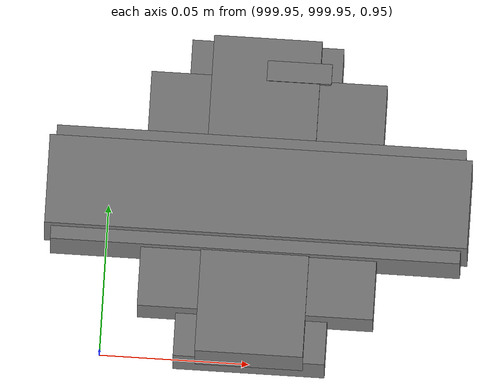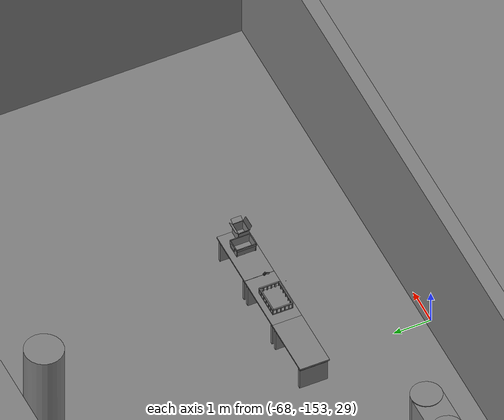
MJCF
<mujoco>
    <option gravity="0.000000000 0.000000000 -9.810000420" timestep="0.0049999999" integrator="implicitfast" density="1.225" viscosity="1.8000001e-05" noslip_iterations="10" iterations="100" sdf_iterations="50">
        <flag multiccd="disable"/>
    </option>
    <size memory="1000M"/>
    <compiler coordinate="local"/>
    <worldbody>
        <light cutoff="30" pos="0 1 1" dir="0 -1 -2"/>
        <light cutoff="30" pos="0 -1 1" dir="0 1 -2"/>
        <body pos="-66.052619934 -149.323638916 31.164688110" euler="-79.375839233 38.863784790 -165.416961670" mocap="true" name="spotlight4_SpotLight"/>
        <body pos="1000.000000000 1000.000000000 1.000000000" euler="0.000000000 0.000000000 180.000000000" name="openloong_gripper_2f85_fix_base_usda_battery_01">
            <geom contype="1" conaffinity="1" density="1000" type="box" material="" rgba="0.500000000 0.500000000 0.500000000 1.000000000" solimp="0.899999976 0.949999988 0.001000000" friction="1.000000000 0.005000000 0.000100000" solref="0.020000000 1.000000000" margin="0" condim="3" group="0" pos="-0.011123657 -0.041940309 0.101691343" quat="1.000000000 0.000000000 0.000000000 0.000000000" size="0.010800000 0.003375000 0.004725000" name="openloong_gripper_2f85_fix_base_usda_geom_733079EA_CDD8_407D_A23B_3CA306F48DB6"/>
            <geom contype="1" conaffinity="1" density="1000" type="box" material="" rgba="0.500000000 0.500000000 0.500000000 1.000000000" solimp="0.899999976 0.949999988 0.001000000" friction="1.000000000 0.005000000 0.000100000" solref="0.020000000 1.000000000" margin="0" condim="3" group="0" pos="-0.010876465 -0.044247437 0.047066893" quat="0.998702705 -0.050920475 0.000000000 0.000000000" size="0.009450001 0.002700000 0.024975000" name="openloong_gripper_2f85_fix_base_usda_geom_F40EDBBE_2A4A_42DC_97B9_01E76797F5F6"/>
            <geom contype="1" conaffinity="1" density="1000" type="box" material="" rgba="0.500000000 0.500000000 0.500000000 1.000000000" solimp="0.899999976 0.949999988 0.001000000" friction="1.000000000 0.005000000 0.000100000" solref="0.020000000 1.000000000" margin="0" condim="3" group="0" pos="-0.001235962 -0.000659180 0.047381196" quat="1.000000000 0.000000000 0.000000000 0.000000000" size="0.039420001 0.039150000 0.047250003" name="openloong_gripper_2f85_fix_base_usda_geom_BE02DAC7_E18F_4A39_B016_0D5C3B3B2CBA"/>
            <geom contype="1" conaffinity="1" density="1000" type="box" material="" rgba="0.500000000 0.500000000 0.500000000 1.000000000" solimp="0.899999976 0.949999988 0.001000000" friction="1.000000000 0.005000000 0.000100000" solref="0.020000000 1.000000000" margin="0" condim="3" group="0" pos="-0.010876465 -0.039138794 0.009851727" quat="1.000000000 0.000000000 0.000000000 0.000000000" size="0.009450001 0.010800000 0.013500000" name="openloong_gripper_2f85_fix_base_usda_geom_02BEEF45_7ABE_4045_BBFF_22CED882FE13"/>
            <geom contype="1" conaffinity="1" density="1000" type="box" material="" rgba="0.500000000 0.500000000 0.500000000 1.000000000" solimp="0.899999976 0.949999988 0.001000000" friction="1.000000000 0.005000000 0.000100000" solref="0.020000000 1.000000000" margin="0" condim="3" group="0" pos="-0.010876465 -0.041528322 0.071508206" quat="1.000000000 0.000000000 0.000000000 0.000000000" size="0.009450001 0.002700000 0.027000001" name="openloong_gripper_2f85_fix_base_usda_geom_2DD57E76_6DCD_4E99_AC76_CDA43B74FFA4"/>
            <freejoint name="openloong_gripper_2f85_fix_base_usda_battery_01_joint"/>
            <site size="0.005000000 0.005000000 0.005000000" rgba="0.500000000 0.500000000 0.500000000 1.000000000" pos="0.000000000 0.000000000 0.000000000" quat="0.999961913 0.008726500 0.000000000 0.000000000" group="0" type="sphere" name="openloong_gripper_2f85_fix_base_usda_battery_01site"/>
        </body>
        <body pos="-65.941947937 -149.348907471 31.171623230" euler="121.385459900 -79.244842529 -5.503401279" mocap="true" name="spotlight3_SpotLight"/>
        <body pos="1000.000000000 1000.000000000 1.000000000" euler="0.000000000 0.000000000 180.000000000" name="openloong_gripper_2f85_fix_base_usda_cpu_fan">
            <geom contype="1" conaffinity="1" density="1000" type="box" material="" rgba="0.500000000 0.500000000 0.500000000 1.000000000" solimp="0.899999976 0.949999988 0.001000000" friction="1.000000000 0.005000000 0.000100000" solref="0.020000000 1.000000000" margin="0" condim="3" group="0" pos="0.000000000 0.000000000 0.070034981" quat="0.000000000 0.000000000 0.000000000 1.000000000" size="0.070700005 0.014699999 0.070700005" name="openloong_gripper_2f85_fix_base_usda_geom_BFCD2B3F_1D78_40E5_8D65_1744A8304FCE"/>
            <freejoint name="openloong_gripper_2f85_fix_base_usda_cpu_fan_joint"/>
            <site size="0.005000000 0.005000000 0.005000000" rgba="0.500000000 0.500000000 0.500000000 1.000000000" pos="0.000000000 0.000000000 0.000000000" quat="0.999961913 0.008726535 0.000000000 0.000000000" group="0" type="sphere" name="openloong_gripper_2f85_fix_base_usda_cpu_fancsite"/>
        </body>
        <body pos="1000.000000000 1000.000000000 1.000000000" euler="0.000000000 0.000000000 180.000000000" name="openloong_gripper_2f85_fix_base_usda_wifi_box">
            <geom contype="1" conaffinity="1" density="1000" type="box" material="" rgba="0.500000000 0.500000000 0.500000000 1.000000000" solimp="0.899999976 0.949999988 0.001000000" friction="1.000000000 0.005000000 0.000100000" solref="0.020000000 1.000000000" margin="0" condim="3" group="0" pos="0.000000000 0.000000000 0.058978677" quat="0.000000000 0.000000047 0.000000000 1.000000000" size="0.068499997 0.018999999 0.059000000" name="openloong_gripper_2f85_fix_base_usda_geom_3BC51305_CF48_4FD3_BEEA_6374C80A53A0"/>
            <freejoint name="openloong_gripper_2f85_fix_base_usda_wifi_box_joint"/>
            <site size="0.005000000 0.005000000 0.005000000" rgba="0.500000000 0.500000000 0.500000000 1.000000000" pos="0.000000000 0.000000000 0.000000000" quat="0.999961913 0.008726500 0.000000000 0.000000000" group="0" type="sphere" name="openloong_gripper_2f85_fix_base_usda_wifi_boxsite"/>
        </body>
        <body pos="1000.000000000 1000.000000000 1.000000000" euler="0.000011953 0.000005123 -179.999984741" name="openloong_gripper_2f85_fix_base_usda_intel_box">
            <geom contype="1" conaffinity="1" density="1000" type="box" material="" rgba="0.500000000 0.500000000 0.500000000 1.000000000" solimp="0.899999976 0.949999988 0.001000000" friction="1.000000000 0.005000000 0.000100000" solref="0.020000000 1.000000000" margin="0" condim="3" group="0" pos="0.000000000 -0.000067139 0.000082284" quat="0.707106709 0.000000225 0.000000253 0.707106650" size="0.052800003 0.025300000 0.052800003" name="openloong_gripper_2f85_fix_base_usda_geom_977555B2_5BA8_4DE6_BC0A_EC29DABA850F"/>
            <freejoint name="openloong_gripper_2f85_fix_base_usda_intel_box_joint"/>
            <site size="0.005000000 0.005000000 0.005000000" rgba="0.500000000 0.500000000 0.500000000 1.000000000" pos="0.000000000 0.000000000 0.000000000" quat="0.999961913 0.008726500 0.000000000 0.000000000" group="0" type="sphere" name="openloong_gripper_2f85_fix_base_usda_intel_boxsite"/>
        </body>
        <body pos="1000.000000000 999.999938965 1.000000000" euler="0.000000000 0.000000000 180.000000000" name="openloong_gripper_2f85_fix_base_usda_intelcore_i5">
            <geom contype="1" conaffinity="1" density="1000" type="box" material="" rgba="0.500000000 0.500000000 0.500000000 1.000000000" solimp="0.899999976 0.949999988 0.001000000" friction="1.000000000 0.005000000 0.000100000" solref="0.020000000 1.000000000" margin="0" condim="3" group="0" pos="0.000000000 0.000000000 0.051722717" quat="0.707106709 0.000000000 0.000000000 -0.707106769" size="0.052800000 0.018080002 0.052800000" name="openloong_gripper_2f85_fix_base_usda_geom_A2586AA4_F103_44C0_B1FF_E666C8D6EDD7"/>
            <freejoint name="openloong_gripper_2f85_fix_base_usda_intelcore_i5_joint"/>
            <site size="0.005000000 0.005000000 0.005000000" rgba="0.500000000 0.500000000 0.500000000 1.000000000" pos="0.000000000 0.000000000 0.000000000" quat="0.999961913 0.008726534 0.000000000 0.000000000" group="0" type="sphere" name="openloong_gripper_2f85_fix_base_usda_intelcore_i5site"/>
        </body>
        <body pos="-65.916450500 -149.759063721 31.162296295" euler="106.695510864 -24.525480270 -6.589144230" mocap="true" name="spotlight2_SpotLight"/>
        <body pos="-64.866622925 -149.383972168 30.183746338" euler="89.999984741 89.999946594 0.000000000" name="openloong_gripper_2f85_fix_base_usda_bluebox_01">
            <geom contype="1" conaffinity="1" density="1000" type="box" material="" rgba="0.500000000 0.500000000 0.500000000 1.000000000" solimp="0.899999976 0.949999988 0.001000000" friction="1.000000000 0.005000000 0.000100000" solref="0.020000000 1.000000000" margin="0" condim="3" group="0" pos="0.276580811 0.187225342 0.000068665" quat="0.707106948 0.000077471 0.707106352 0.000077486" size="0.100000001 0.057999998 0.010000000" name="openloong_gripper_2f85_fix_base_usda_geom_860AC683_E3D6_4E0D_B5B7_23EA4D80CF23"/>
            <geom contype="1" conaffinity="1" density="1000" type="box" material="" rgba="0.500000000 0.500000000 0.500000000 1.000000000" solimp="0.899999976 0.949999988 0.001000000" friction="1.000000000 0.005000000 0.000100000" solref="0.020000000 1.000000000" margin="0" condim="3" group="0" pos="0.000000000 0.002883911 0.000000000" quat="0.999999881 0.000000000 0.000000000 0.000000000" size="0.254000008 0.003000000 0.172000006" name="openloong_gripper_2f85_fix_base_usda_geom_A0805E65_2570_4196_BB57_26D129A16275"/>
            <geom contype="1" conaffinity="1" density="1000" type="box" material="" rgba="0.500000000 0.500000000 0.500000000 1.000000000" solimp="0.899999976 0.949999988 0.001000000" friction="1.000000000 0.005000000 0.000100000" solref="0.020000000 1.000000000" margin="0" condim="3" group="0" pos="0.000000000 0.124874115 0.173484802" quat="0.999796331 0.020176515 -0.000000015 0.000000030" size="0.259999990 0.119999997 0.007000000" name="openloong_gripper_2f85_fix_base_usda_geom_D3C1B3C0_0353_49E7_94AA_141300C4FCC8"/>
            <geom contype="1" conaffinity="1" density="1000" type="box" material="" rgba="0.500000000 0.500000000 0.500000000 1.000000000" solimp="0.899999976 0.949999988 0.001000000" friction="1.000000000 0.005000000 0.000100000" solref="0.020000000 1.000000000" margin="0" condim="3" group="0" pos="0.000000000 0.124874115 -0.173469543" quat="0.999796331 -0.020176545 -0.000000015 0.000000000" size="0.259999990 0.119999997 0.007000000" name="openloong_gripper_2f85_fix_base_usda_geom_AB0C867C_19D5_4290_9F88_DD0108D918CC"/>
            <geom contype="1" conaffinity="1" density="1000" type="box" material="" rgba="0.500000000 0.500000000 0.500000000 1.000000000" solimp="0.899999976 0.949999988 0.001000000" friction="1.000000000 0.005000000 0.000100000" solref="0.020000000 1.000000000" margin="0" condim="3" group="0" pos="0.000000000 0.214008331 0.188980103" quat="0.999912977 0.013176724 0.000000015 0.000000000" size="0.259999990 0.029999999 0.012500000" name="openloong_gripper_2f85_fix_base_usda_geom_199C3EF8_4371_46FD_AA15_F8527515D536"/>
            <geom contype="1" conaffinity="1" density="1000" type="box" material="" rgba="0.500000000 0.500000000 0.500000000 1.000000000" solimp="0.899999976 0.949999988 0.001000000" friction="1.000000000 0.005000000 0.000100000" solref="0.020000000 1.000000000" margin="0" condim="3" group="0" pos="-0.258361816 0.125289917 0.001876831" quat="0.702796936 -0.020792112 0.710783124 0.020769298" size="0.189999998 0.119999997 0.009000000" name="openloong_gripper_2f85_fix_base_usda_geom_2E488D78_A6A1_44D3_99F6_5AD35E9960FF"/>
            <geom contype="1" conaffinity="1" density="1000" type="box" material="" rgba="0.500000000 0.500000000 0.500000000 1.000000000" solimp="0.899999976 0.949999988 0.001000000" friction="1.000000000 0.005000000 0.000100000" solref="0.020000000 1.000000000" margin="0" condim="3" group="0" pos="0.000000000 0.214008331 -0.188980103" quat="0.999912977 -0.013176769 0.000000030 0.000000015" size="0.259999990 0.029999999 0.012500000" name="openloong_gripper_2f85_fix_base_usda_geom_C77CCF72_54D1_4E27_A974_4A8452B93F72"/>
            <geom contype="1" conaffinity="1" density="1000" type="box" material="" rgba="0.500000000 0.500000000 0.500000000 1.000000000" solimp="0.899999976 0.949999988 0.001000000" friction="1.000000000 0.005000000 0.000100000" solref="0.020000000 1.000000000" margin="0" condim="3" group="0" pos="-0.276611328 0.187225342 0.000068665" quat="0.707106650 0.000077441 0.707106709 0.000077456" size="0.100000001 0.057999998 0.010000000" name="openloong_gripper_2f85_fix_base_usda_geom_B094E169_E7C3_4F3B_B427_4AC8968B96FC"/>
            <geom contype="1" conaffinity="1" density="1000" type="box" material="" rgba="0.500000000 0.500000000 0.500000000 1.000000000" solimp="0.899999976 0.949999988 0.001000000" friction="1.000000000 0.005000000 0.000100000" solref="0.020000000 1.000000000" margin="0" condim="3" group="0" pos="0.258331299 0.125289917 0.001876831" quat="0.702851415 0.018856421 0.710823774 -0.019329369" size="0.189999998 0.119999997 0.009000000" name="openloong_gripper_2f85_fix_base_usda_geom_18201E09_758E_4A7E_84CE_CB2A7C98B544"/>
            <freejoint name="openloong_gripper_2f85_fix_base_usda_bluebox_01_joint"/>
            <site size="0.005000000 0.005000000 0.005000000" rgba="0.500000000 0.500000000 0.500000000 1.000000000" pos="0.000000000 0.000000000 0.000000000" quat="0.999961913 0.008726534 0.000000000 0.000000000" group="0" type="sphere" name="openloong_gripper_2f85_fix_base_usda_bluebox_01site"/>
        </body>
        <body pos="-64.496299744 -149.491867065 30.235729218" euler="0.000000000 0.000000000 89.999946594" name="openloong_gripper_2f85_fix_base_usda_cardboardbox_01">
            <geom contype="1" conaffinity="1" density="1000" type="box" material="" rgba="0.500000000 0.500000000 0.500000000 1.000000000" solimp="0.899999976 0.949999988 0.001000000" friction="1.000000000 0.005000000 0.000100000" solref="0.020000000 1.000000000" margin="0" condim="3" group="0" pos="-0.003166199 -0.004086494 0.005052090" quat="1.000000000 0.000000000 0.000000000 0.000000000" size="0.142499998 0.177500010 0.005000000" name="openloong_gripper_2f85_fix_base_usda_geom_85AEAF62_A2A4_433B_81ED_A8290131A12F"/>
            <geom contype="1" conaffinity="1" density="1000" type="box" material="" rgba="0.500000000 0.500000000 0.500000000 1.000000000" solimp="0.899999976 0.949999988 0.001000000" friction="1.000000000 0.005000000 0.000100000" solref="0.020000000 1.000000000" margin="0" condim="3" group="0" pos="-0.003166199 0.170316696 0.150570869" quat="1.000000000 0.000000000 0.000000000 0.000000000" size="0.142499998 0.005000000 0.149999991" name="openloong_gripper_2f85_fix_base_usda_geom_DC1BF9E8_B475_45ED_81B8_74CB25DEF167"/>
            <geom contype="1" conaffinity="1" density="1000" type="box" material="" rgba="0.500000000 0.500000000 0.500000000 1.000000000" solimp="0.899999976 0.949999988 0.001000000" friction="1.000000000 0.005000000 0.000100000" solref="0.020000000 1.000000000" margin="0" condim="3" group="0" pos="-0.147399902 -0.005307198 0.150570869" quat="1.000000000 0.000000000 0.000000000 0.000000000" size="0.005000000 0.177500010 0.149999991" name="openloong_gripper_2f85_fix_base_usda_geom_F5F5192D_6EFF_4028_A544_95823C0DCA8C"/>
            <geom contype="1" conaffinity="1" density="1000" type="box" material="" rgba="0.500000000 0.500000000 0.500000000 1.000000000" solimp="0.899999976 0.949999988 0.001000000" friction="1.000000000 0.005000000 0.000100000" solref="0.020000000 1.000000000" margin="0" condim="3" group="0" pos="0.140275955 -0.005307198 0.150570869" quat="1.000000000 0.000000000 0.000000000 0.000000000" size="0.005000000 0.177500010 0.149999991" name="openloong_gripper_2f85_fix_base_usda_geom_5A4518EC_61F3_4F02_B644_CAC9376A8B6B"/>
            <geom contype="1" conaffinity="1" density="1000" type="box" material="" rgba="0.500000000 0.500000000 0.500000000 1.000000000" solimp="0.899999976 0.949999988 0.001000000" friction="1.000000000 0.005000000 0.000100000" solref="0.020000000 1.000000000" margin="0" condim="3" group="0" pos="-0.003166199 -0.181550980 0.150570869" quat="1.000000000 0.000000000 0.000000000 0.000000000" size="0.142499998 0.005000000 0.149999991" name="openloong_gripper_2f85_fix_base_usda_geom_0EE234DB_E685_4A31_AF1B_905F86F97FFD"/>
            <freejoint name="openloong_gripper_2f85_fix_base_usda_cardboardbox_01_joint"/>
            <site size="0.005000000 0.005000000 0.005000000" rgba="0.500000000 0.500000000 0.500000000 1.000000000" pos="0.000000000 0.000000000 0.000000000" quat="0.999961913 0.008726535 0.000000000 0.000000000" group="0" type="sphere" name="openloong_gripper_2f85_fix_base_usda_site_F26D7ABC_35A5_471E_B480_2E2FCFEF28D6"/>
            <body pos="0.139160156 -0.004048347 0.301930904" euler="-179.999954224 49.383502960 179.999954224" name="openloong_gripper_2f85_fix_base_usda_A1_006">
                <geom contype="1" conaffinity="1" density="1000" type="box" material="" rgba="0.500000000 0.500000000 0.500000000 1.000000000" solimp="0.899999976 0.949999988 0.001000000" friction="1.000000000 0.005000000 0.000100000" solref="0.020000000 1.000000000" margin="0" condim="3" group="0" pos="-0.071587563 0.000009537 0.001745224" quat="0.999999881 0.000000000 0.000000000 0.000000000" size="0.071249999 0.179999992 0.002500000" name="openloong_gripper_2f85_fix_base_usda_geom_08D82171_4718_4A84_81F4_3AAE935F9436"/>
                <joint armature="0" stiffness="0.07" damping="0.0099999998" axis="0.000000 1.000000 0.000000" type="hinge" name="openloong_gripper_2f85_fix_base_usda_A1_006"/>
            </body>
            <body pos="-0.145902634 -0.004086494 0.301938057" euler="-180.000000000 -60.000011444 -180.000000000" name="openloong_gripper_2f85_fix_base_usda_A2_006">
                <geom contype="1" conaffinity="1" density="1000" type="box" material="" rgba="0.500000000 0.500000000 0.500000000 1.000000000" solimp="0.899999976 0.949999988 0.001000000" friction="1.000000000 0.005000000 0.000100000" solref="0.020000000 1.000000000" margin="0" condim="3" group="0" pos="0.071268082 0.000009537 0.002717972" quat="0.000002921 0.000000000 -0.000000030 0.999999881" size="0.071249999 0.179999992 0.002500000" name="openloong_gripper_2f85_fix_base_usda_geom_29788015_BACA_49CB_8AC7_22ECBBDEA13B"/>
                <joint armature="0" stiffness="0.07" damping="0.0099999998" axis="0.000000 1.000000 0.000000" type="hinge" name="openloong_gripper_2f85_fix_base_usda_A2_006"/>
            </body>
            <body pos="-0.003385544 0.175991058 0.301930904" euler="-125.858116150 -0.000004561 0.000002331" name="openloong_gripper_2f85_fix_base_usda_B2_006">
                <geom contype="1" conaffinity="1" density="1000" type="box" material="" rgba="0.500000000 0.500000000 0.500000000 1.000000000" solimp="0.899999976 0.949999988 0.001000000" friction="1.000000000 0.005000000 0.000100000" solref="0.020000000 1.000000000" margin="0" condim="3" group="0" pos="0.000009537 -0.070939064 -0.002470016" quat="0.999614120 0.027776197 -0.000000015 0.000000030" size="0.137500003 0.064999998 0.005000000" name="openloong_gripper_2f85_fix_base_usda_geom_6B0EFC9E_3CDE_4116_9B9A_96ECCC537E93"/>
                <joint armature="0" stiffness="0.07" damping="0.0099999998" axis="1.000000 0.000000 0.000000" type="hinge" name="openloong_gripper_2f85_fix_base_usda_B2_006"/>
            </body>
            <body pos="-0.003385544 -0.184140205 0.301938057" euler="147.805557251 0.000000000 0.000000000" name="openloong_gripper_2f85_fix_base_usda_B1_006">
                <geom contype="1" conaffinity="1" density="1000" type="box" material="" rgba="0.500000000 0.500000000 0.500000000 1.000000000" solimp="0.899999976 0.949999988 0.001000000" friction="1.000000000 0.005000000 0.000100000" solref="0.020000000 1.000000000" margin="0" condim="3" group="0" pos="-0.000028610 0.070202351 -0.002703667" quat="0.999614179 -0.027776167 0.000000000 0.000000000" size="0.137500003 0.064999998 0.005000000" name="openloong_gripper_2f85_fix_base_usda_geom_B2B06439_E840_4972_B6AC_CF3B943F9DC3"/>
                <joint armature="0" stiffness="0.07" damping="0.0099999998" axis="1.000000 0.000000 0.000000" type="hinge" name="openloong_gripper_2f85_fix_base_usda_B1_006"/>
            </body>
        </body>
        <body pos="-65.882858276 -149.481979370 30.229999542" euler="-64.487716675 0.000000000 0.000000000" name="openloong_gripper_2f85_fix_base_usda_Barcode">
            <geom contype="1" conaffinity="1" density="1000" type="box" material="" rgba="0.500000000 0.500000000 0.500000000 1.000000000" solimp="0.899999976 0.949999988 0.001000000" friction="1.000000000 0.005000000 0.000100000" solref="0.020000000 1.000000000" margin="0" condim="3" group="0" pos="0.000000000 0.013038635 0.001419067" quat="0.000000000 0.000000000 0.000000000 1.000000119" size="0.034000002 0.010000000 0.017999999" name="openloong_gripper_2f85_fix_base_usda_geom_1DD97D0C_7CEB_46F1_B640_450B31EBB238"/>
            <geom contype="1" conaffinity="1" density="1000" type="box" material="" rgba="0.500000000 0.500000000 0.500000000 1.000000000" solimp="0.899999976 0.949999988 0.001000000" friction="1.000000000 0.005000000 0.000100000" solref="0.020000000 1.000000000" margin="0" condim="3" group="0" pos="0.000000000 -0.035301208 -0.007095337" quat="0.000000000 0.000000000 -0.043619365 0.999048233" size="0.028999999 0.010000000 0.020000000" name="openloong_gripper_2f85_fix_base_usda_geom_D227DC62_02AE_4D6D_ABAA_174EEA33F704"/>
            <geom contype="1" conaffinity="1" density="1000" type="box" material="" rgba="0.500000000 0.500000000 0.500000000 1.000000000" solimp="0.899999976 0.949999988 0.001000000" friction="1.000000000 0.005000000 0.000100000" solref="0.020000000 1.000000000" margin="0" condim="3" group="0" pos="0.000000000 -0.043411255 -0.011749268" quat="0.922262907 0.386563420 0.000000000 0.000000000" size="0.026000001 0.010000000 0.020000000" name="openloong_gripper_2f85_fix_base_usda_geom_03952D01_50D4_49F2_BE6B_9A7A1F00D2E9"/>
            <geom contype="1" conaffinity="1" density="1000" type="box" material="" rgba="0.500000000 0.500000000 0.500000000 1.000000000" solimp="0.899999976 0.949999988 0.001000000" friction="1.000000000 0.005000000 0.000100000" solref="0.020000000 1.000000000" margin="0" condim="3" group="0" pos="0.000000000 -0.016967773 -0.031860352" quat="0.000000000 0.000000000 0.000000000 1.000000119" size="0.008000000 0.010000000 0.013000000" name="openloong_gripper_2f85_fix_base_usda_geom_02203DD0_405C_4447_9324_D7E430F6D2A2"/>
            <geom contype="1" conaffinity="1" density="1000" type="box" material="" rgba="0.500000000 0.500000000 0.500000000 1.000000000" solimp="0.899999976 0.949999988 0.001000000" friction="1.000000000 0.005000000 0.000100000" solref="0.020000000 1.000000000" margin="0" condim="3" group="0" pos="0.000000000 -0.001869202 0.000312805" quat="0.953716993 0.300705761 0.000000000 0.000000000" size="0.032000002 0.010000000 0.018999999" name="openloong_gripper_2f85_fix_base_usda_geom_5DA143D4_91F5_49F1_8E5C_50201547B485"/>
            <geom contype="1" conaffinity="1" density="1000" type="box" material="" rgba="0.500000000 0.500000000 0.500000000 1.000000000" solimp="0.899999976 0.949999988 0.001000000" friction="1.000000000 0.005000000 0.000100000" solref="0.020000000 1.000000000" margin="0" condim="3" group="0" pos="0.000000000 -0.019531250 -0.003173828" quat="0.953716993 0.300705761 0.000000000 0.000000000" size="0.030999999 0.010000000 0.020000000" name="openloong_gripper_2f85_fix_base_usda_geom_B62ACB7B_8443_4113_9ABB_7BA82BF1DB7D"/>
            <geom contype="1" conaffinity="1" density="1000" type="box" material="" rgba="0.500000000 0.500000000 0.500000000 1.000000000" solimp="0.899999976 0.949999988 0.001000000" friction="1.000000000 0.005000000 0.000100000" solref="0.020000000 1.000000000" margin="0" condim="3" group="0" pos="0.000000000 -0.035301208 -0.007095337" quat="0.953716993 0.300705761 0.000000000 0.000000000" size="0.028999999 0.010000000 0.020000000" name="openloong_gripper_2f85_fix_base_usda_geom_8F80B376_5BE3_472F_9903_17B187EB2418"/>
            <geom contype="1" conaffinity="1" density="1000" type="box" material="" rgba="0.500000000 0.500000000 0.500000000 1.000000000" solimp="0.899999976 0.949999988 0.001000000" friction="1.000000000 0.005000000 0.000100000" solref="0.020000000 1.000000000" margin="0" condim="3" group="0" pos="0.000000000 -0.042617798 -0.071121216" quat="0.000000000 0.000000000 0.000000000 1.000000119" size="0.013000000 0.021000000 0.059999999" name="openloong_gripper_2f85_fix_base_usda_geom_B6433BA4_C9CA_4A15_8DC5_A873936CD823"/>
            <freejoint name="openloong_gripper_2f85_fix_base_usda_Barcode_joint"/>
            <site size="0.005000000 0.005000000 0.005000000" rgba="0.500000000 0.500000000 0.500000000 1.000000000" pos="0.000000000 0.000000000 0.000000000" quat="1.000000000 0.000000000 0.000000000 0.000000000" group="0" type="sphere" name="openloong_gripper_2f85_fix_base_usda_Barcode_site"/>
        </body>
        <body pos="-66.745018005 -149.392349243 30.184000015" euler="0.000000000 0.000000000 89.999946594" name="[22329902261816]_Basket_01">
            <geom contype="1" conaffinity="1" density="1000" type="box" material="" rgba="0.500000000 0.500000000 0.500000000 1.000000000" solimp="0.899999976 0.949999988 0.001000000" friction="1.000000000 0.005000000 0.000100000" solref="0.020000000 1.000000000" margin="0" condim="3" group="0" pos="-0.052425385 0.389207840 0.089787483" quat="0.707107008 0.000000000 0.000000000 0.707106411" size="0.014249999 0.014249999 0.059999999" name="[22329902261816]_geom_64A699BF_0299_47A5_9B85_E9E7C9E14B06"/>
            <geom contype="1" conaffinity="1" density="1000" type="box" material="" rgba="0.500000000 0.500000000 0.500000000 1.000000000" solimp="0.899999976 0.949999988 0.001000000" friction="1.000000000 0.005000000 0.000100000" solref="0.020000000 1.000000000" margin="0" condim="3" group="0" pos="0.264015198 -0.133043289 0.089787483" quat="0.707107008 0.000000000 0.000000000 0.707106411" size="0.014249999 0.014249999 0.059999999" name="[22329902261816]_geom_C1CB3E9D_D331_4A25_AAD1_AF1922AFF084"/>
            <geom contype="1" conaffinity="1" density="1000" type="box" material="" rgba="0.500000000 0.500000000 0.500000000 1.000000000" solimp="0.899999976 0.949999988 0.001000000" friction="1.000000000 0.005000000 0.000100000" solref="0.020000000 1.000000000" margin="0" condim="3" group="0" pos="-0.264015198 -0.265548706 0.089793205" quat="0.707107008 0.000000000 0.000000000 0.707106411" size="0.014249999 0.014249999 0.059999999" name="[22329902261816]_geom_C704D089_1CAD_44CB_A57E_030F3F83E342"/>
            <geom contype="1" conaffinity="1" density="1000" type="box" material="" rgba="0.500000000 0.500000000 0.500000000 1.000000000" solimp="0.899999976 0.949999988 0.001000000" friction="1.000000000 0.005000000 0.000100000" solref="0.020000000 1.000000000" margin="0" condim="3" group="0" pos="-0.160263062 -0.389322281 0.089793205" quat="0.707107008 0.000000000 0.000000000 0.707106411" size="0.014249999 0.014249999 0.059999999" name="[22329902261816]_geom_023551AB_6829_4E47_9ABF_DB6311E00616"/>
            <geom contype="1" conaffinity="1" density="1000" type="box" material="" rgba="0.500000000 0.500000000 0.500000000 1.000000000" solimp="0.899999976 0.949999988 0.001000000" friction="1.000000000 0.005000000 0.000100000" solref="0.020000000 1.000000000" margin="0" condim="3" group="0" pos="0.162265778 -0.389322281 0.089787483" quat="0.707107008 0.000000000 0.000000000 0.707106411" size="0.014249999 0.014249999 0.059999999" name="[22329902261816]_geom_B4F81383_0213_434D_97DB_54739A89312B"/>
            <geom contype="1" conaffinity="1" density="1000" type="box" material="" rgba="0.500000000 0.500000000 0.500000000 1.000000000" solimp="0.899999976 0.949999988 0.001000000" friction="1.000000000 0.005000000 0.000100000" solref="0.020000000 1.000000000" margin="0" condim="3" group="0" pos="0.264015198 0.389207840 0.089787483" quat="0.707107008 0.000000000 0.000000000 0.707106411" size="0.014249999 0.014249999 0.059999999" name="[22329902261816]_geom_DD466C6F_6EB8_4B91_A07E_95C308AAF6CC"/>
            <geom contype="1" conaffinity="1" density="1000" type="box" material="" rgba="0.500000000 0.500000000 0.500000000 1.000000000" solimp="0.899999976 0.949999988 0.001000000" friction="1.000000000 0.005000000 0.000100000" solref="0.020000000 1.000000000" margin="0" condim="3" group="0" pos="-0.264015198 -0.133043289 0.089793205" quat="0.707107008 0.000000000 0.000000000 0.707106411" size="0.014249999 0.014249999 0.059999999" name="[22329902261816]_geom_4F62C2D6_3EA4_45B5_ADDC_F3C5EDC3A24D"/>
            <geom contype="1" conaffinity="1" density="1000" type="box" material="" rgba="0.500000000 0.500000000 0.500000000 1.000000000" solimp="0.899999976 0.949999988 0.001000000" friction="1.000000000 0.005000000 0.000100000" solref="0.020000000 1.000000000" margin="0" condim="3" group="0" pos="-0.264026642 0.269256592 0.089793205" quat="0.707107008 0.000000000 0.000000000 0.707106411" size="0.014249999 0.014249999 0.059999999" name="[22329902261816]_geom_A5455A19_3899_4B7C_9E4D_F553F6A66D76"/>
            <geom contype="1" conaffinity="1" density="1000" type="box" material="" rgba="0.500000000 0.500000000 0.500000000 1.000000000" solimp="0.899999976 0.949999988 0.001000000" friction="1.000000000 0.005000000 0.000100000" solref="0.020000000 1.000000000" margin="0" condim="3" group="0" pos="0.054462433 0.389207840 0.089787483" quat="0.707107008 0.000000000 0.000000000 0.707106411" size="0.014249999 0.014249999 0.059999999" name="[22329902261816]_geom_19307FA2_59E5_4193_B867_22717E218CCC"/>
            <geom contype="1" conaffinity="1" density="1000" type="box" material="" rgba="0.500000000 0.500000000 0.500000000 1.000000000" solimp="0.899999976 0.949999988 0.001000000" friction="1.000000000 0.005000000 0.000100000" solref="0.020000000 1.000000000" margin="0" condim="3" group="0" pos="0.054462433 -0.389322281 0.089787483" quat="0.707107008 0.000000000 0.000000000 0.707106411" size="0.014249999 0.014249999 0.059999999" name="[22329902261816]_geom_F0C78F65_8C22_406D_9DBE_BC41A0886ABA"/>
            <geom contype="1" conaffinity="1" density="1000" type="box" material="" rgba="0.500000000 0.500000000 0.500000000 1.000000000" solimp="0.899999976 0.949999988 0.001000000" friction="1.000000000 0.005000000 0.000100000" solref="0.020000000 1.000000000" margin="0" condim="3" group="0" pos="0.264015198 0.269256592 0.089793205" quat="0.707107008 0.000000000 0.000000000 0.707106411" size="0.014249999 0.014249999 0.059999999" name="[22329902261816]_geom_718D97AA_6393_42B9_9F76_80A151DE4571"/>
            <geom contype="1" conaffinity="1" density="1000" type="box" material="" rgba="0.500000000 0.500000000 0.500000000 1.000000000" solimp="0.899999976 0.949999988 0.001000000" friction="1.000000000 0.005000000 0.000100000" solref="0.020000000 1.000000000" margin="0" condim="3" group="0" pos="0.264015198 -0.389322281 0.089787483" quat="0.707107008 0.000000000 0.000000000 0.707106411" size="0.014249999 0.014249999 0.059999999" name="[22329902261816]_geom_04A46C0D_3861_4220_A4E9_5FEC3A087B66"/>
            <geom contype="1" conaffinity="1" density="1000" type="box" material="" rgba="0.500000000 0.500000000 0.500000000 1.000000000" solimp="0.899999976 0.949999988 0.001000000" friction="1.000000000 0.005000000 0.000100000" solref="0.020000000 1.000000000" margin="0" condim="3" group="0" pos="0.000000000 0.000000000 0.015998840" quat="0.707107008 0.000000000 0.000000000 0.707106411" size="0.403499991 0.279000014 0.015750000" name="[22329902261816]_geom_C62C2F18_7FD1_48D2_B11C_F2D149B0F680"/>
            <geom contype="1" conaffinity="1" density="1000" type="box" material="" rgba="0.500000000 0.500000000 0.500000000 1.000000000" solimp="0.899999976 0.949999988 0.001000000" friction="1.000000000 0.005000000 0.000100000" solref="0.020000000 1.000000000" margin="0" condim="3" group="0" pos="0.000000000 -0.389476776 0.163619041" quat="0.707107008 0.000000000 0.000000000 0.707106411" size="0.015000000 0.277500004 0.015750000" name="[22329902261816]_geom_3B7D78DB_D27B_4161_8F3B_877E80F07355"/>
            <geom contype="1" conaffinity="1" density="1000" type="box" material="" rgba="0.500000000 0.500000000 0.500000000 1.000000000" solimp="0.899999976 0.949999988 0.001000000" friction="1.000000000 0.005000000 0.000100000" solref="0.020000000 1.000000000" margin="0" condim="3" group="0" pos="0.162265778 0.389207840 0.089787483" quat="0.707107008 0.000000000 0.000000000 0.707106411" size="0.014249999 0.014249999 0.059999999" name="[22329902261816]_geom_2F80F431_77CE_4FB0_A806_9DFF737F19CA"/>
            <geom contype="1" conaffinity="1" density="1000" type="box" material="" rgba="0.500000000 0.500000000 0.500000000 1.000000000" solimp="0.899999976 0.949999988 0.001000000" friction="1.000000000 0.005000000 0.000100000" solref="0.020000000 1.000000000" margin="0" condim="3" group="0" pos="0.000000000 0.389471054 0.163619041" quat="0.707107008 0.000000000 0.000000000 0.707106411" size="0.015000000 0.277500004 0.015750000" name="[22329902261816]_geom_96B5486C_CEB4_4101_9786_A5AA5054B02E"/>
            <geom contype="1" conaffinity="1" density="1000" type="box" material="" rgba="0.500000000 0.500000000 0.500000000 1.000000000" solimp="0.899999976 0.949999988 0.001000000" friction="1.000000000 0.005000000 0.000100000" solref="0.020000000 1.000000000" margin="0" condim="3" group="0" pos="-0.263511658 0.000000000 0.163619041" quat="0.707107008 0.000000000 0.000000000 0.707106411" size="0.403499991 0.015000000 0.015750000" name="[22329902261816]_geom_4AB91861_E464_4F68_B022_5D47E0EC24C9"/>
            <geom contype="1" conaffinity="1" density="1000" type="box" material="" rgba="0.500000000 0.500000000 0.500000000 1.000000000" solimp="0.899999976 0.949999988 0.001000000" friction="1.000000000 0.005000000 0.000100000" solref="0.020000000 1.000000000" margin="0" condim="3" group="0" pos="-0.264015198 0.141334534 0.089793205" quat="0.707107008 0.000000000 0.000000000 0.707106411" size="0.014249999 0.014249999 0.059999999" name="[22329902261816]_geom_85BAD835_523F_4A38_9686_96375EE8A5C9"/>
            <geom contype="1" conaffinity="1" density="1000" type="box" material="" rgba="0.500000000 0.500000000 0.500000000 1.000000000" solimp="0.899999976 0.949999988 0.001000000" friction="1.000000000 0.005000000 0.000100000" solref="0.020000000 1.000000000" margin="0" condim="3" group="0" pos="0.264015198 -0.265548706 0.089787483" quat="0.707107008 0.000000000 0.000000000 0.707106411" size="0.014249999 0.014249999 0.059999999" name="[22329902261816]_geom_979A179A_8561_4414_9BD6_EF84EEE24DE8"/>
            <geom contype="1" conaffinity="1" density="1000" type="box" material="" rgba="0.500000000 0.500000000 0.500000000 1.000000000" solimp="0.899999976 0.949999988 0.001000000" friction="1.000000000 0.005000000 0.000100000" solref="0.020000000 1.000000000" margin="0" condim="3" group="0" pos="-0.160263062 0.389207840 0.089787483" quat="0.707107008 0.000000000 0.000000000 0.707106411" size="0.014249999 0.014249999 0.059999999" name="[22329902261816]_geom_5E29C08A_C5A0_4F0E_93AC_0FC6AEE3D5EE"/>
            <geom contype="1" conaffinity="1" density="1000" type="box" material="" rgba="0.500000000 0.500000000 0.500000000 1.000000000" solimp="0.899999976 0.949999988 0.001000000" friction="1.000000000 0.005000000 0.000100000" solref="0.020000000 1.000000000" margin="0" condim="3" group="0" pos="-0.052425385 -0.389322281 0.089787483" quat="0.707107008 0.000000000 0.000000000 0.707106411" size="0.014249999 0.014249999 0.059999999" name="[22329902261816]_geom_63768174_0A59_4FAD_988C_5FCE5BE7797A"/>
            <geom contype="1" conaffinity="1" density="1000" type="box" material="" rgba="0.500000000 0.500000000 0.500000000 1.000000000" solimp="0.899999976 0.949999988 0.001000000" friction="1.000000000 0.005000000 0.000100000" solref="0.020000000 1.000000000" margin="0" condim="3" group="0" pos="-0.264026642 -0.389322281 0.089793205" quat="0.707107008 0.000000000 0.000000000 0.707106411" size="0.014249999 0.014249999 0.059999999" name="[22329902261816]_geom_50A2CD10_D480_447C_B749_DEE28A36252F"/>
            <geom contype="1" conaffinity="1" density="1000" type="box" material="" rgba="0.500000000 0.500000000 0.500000000 1.000000000" solimp="0.899999976 0.949999988 0.001000000" friction="1.000000000 0.005000000 0.000100000" solref="0.020000000 1.000000000" margin="0" condim="3" group="0" pos="0.264015198 0.141334534 0.089787483" quat="0.707107008 0.000000000 0.000000000 0.707106411" size="0.014249999 0.014249999 0.059999999" name="[22329902261816]_geom_CE77A553_90A8_4C43_9F94_99C1C7D45CEE"/>
            <geom contype="1" conaffinity="1" density="1000" type="box" material="" rgba="0.500000000 0.500000000 0.500000000 1.000000000" solimp="0.899999976 0.949999988 0.001000000" friction="1.000000000 0.005000000 0.000100000" solref="0.020000000 1.000000000" margin="0" condim="3" group="0" pos="-0.264015198 0.389207840 0.089793205" quat="0.707107008 0.000000000 0.000000000 0.707106411" size="0.014249999 0.014249999 0.059999999" name="[22329902261816]_geom_20CE831D_2FD8_403C_917A_48578652F485"/>
            <geom contype="1" conaffinity="1" density="1000" type="box" material="" rgba="0.500000000 0.500000000 0.500000000 1.000000000" solimp="0.899999976 0.949999988 0.001000000" friction="1.000000000 0.005000000 0.000100000" solref="0.020000000 1.000000000" margin="0" condim="3" group="0" pos="0.264015198 0.004480362 0.089787483" quat="0.707107008 0.000000000 0.000000000 0.707106411" size="0.014249999 0.014249999 0.059999999" name="[22329902261816]_geom_BEBD7915_355D_4B4B_8A7A_88A6A202017B"/>
            <geom contype="1" conaffinity="1" density="1000" type="box" material="" rgba="0.500000000 0.500000000 0.500000000 1.000000000" solimp="0.899999976 0.949999988 0.001000000" friction="1.000000000 0.005000000 0.000100000" solref="0.020000000 1.000000000" margin="0" condim="3" group="0" pos="0.263694763 -0.000011444 0.163619041" quat="0.707107008 0.000000000 0.000000000 0.707106411" size="0.403499991 0.015000000 0.015750000" name="[22329902261816]_geom_F6846FC3_D65F_494F_8D5E_CE41BA767BE4"/>
            <geom contype="1" conaffinity="1" density="1000" type="box" material="" rgba="0.500000000 0.500000000 0.500000000 1.000000000" solimp="0.899999976 0.949999988 0.001000000" friction="1.000000000 0.005000000 0.000100000" solref="0.020000000 1.000000000" margin="0" condim="3" group="0" pos="-0.264015198 0.004480362 0.089793205" quat="0.707107008 0.000000000 0.000000000 0.707106411" size="0.014249999 0.014249999 0.059999999" name="[22329902261816]_geom_B06C50BC_FF03_42D2_8E78_596C3E634410"/>
            <freejoint name="[22329902261816]_joint_5D99FE67_9891_490C_802A_E0D3A097BE16"/>
        </body>
        <body pos="0.000000000 0.000000000 0.000000000" euler="0.000000000 0.000000000 0.000000000" name="Static Objects_Static Objects">
            <geom contype="1" conaffinity="1" density="1000" type="box" material="" rgba="0.500000000 0.500000000 0.500000000 1.000000000" solimp="0.899999976 0.949999988 0.001000000" friction="1.000000000 0.005000000 0.000100000" solref="0.020000000 1.000000000" margin="0" condim="3" group="0" pos="-67.544113159 -149.365814209 29.727830887" quat="0.500000417 0.499999970 0.499999553 0.499999970" size="0.381000012 0.319999993 0.041000001" name="Static Objects_geom_03E58716_5ACA_4834_B4E2_BC80CF66DF6C"/>
            <geom contype="1" conaffinity="1" density="1000" type="box" material="" rgba="0.500000000 0.500000000 0.500000000 1.000000000" solimp="0.899999976 0.949999988 0.001000000" friction="1.000000000 0.005000000 0.000100000" solref="0.020000000 1.000000000" margin="0" condim="3" group="0" pos="-68.239501953 -149.365814209 30.086868286" quat="0.500000417 0.499999970 0.499999553 0.499999970" size="0.370999992 0.039500002 0.745000005" name="Static Objects_geom_7CE9540E_F272_4EAF_8E63_6794BE7E8CCC"/>
            <geom contype="1" conaffinity="1" density="1000" type="box" material="" rgba="0.500000000 0.500000000 0.500000000 1.000000000" solimp="0.899999976 0.949999988 0.001000000" friction="1.000000000 0.005000000 0.000100000" solref="0.020000000 1.000000000" margin="0" condim="3" group="0" pos="-68.239501953 -149.365814209 30.147235870" quat="0.500000417 0.499999970 0.499999553 0.499999970" size="0.400000006 0.022000000 0.800000012" name="Static Objects_geom_59BF461C_21C2_4D97_966F_77F7D621CCD7"/>
            <geom contype="1" conaffinity="1" density="1000" type="box" material="" rgba="0.500000000 0.500000000 0.500000000 1.000000000" solimp="0.899999976 0.949999988 0.001000000" friction="1.000000000 0.005000000 0.000100000" solref="0.020000000 1.000000000" margin="0" condim="3" group="0" pos="-68.934890747 -149.365814209 29.727830887" quat="0.500000417 0.499999970 0.499999553 0.499999970" size="0.381000012 0.319999993 0.041000001" name="Static Objects_geom_AF9F593E_B031_42CB_825C_C4A1B9877E4B"/>
            <geom contype="1" conaffinity="1" density="1000" type="box" material="" rgba="0.500000000 0.500000000 0.500000000 1.000000000" solimp="0.899999976 0.949999988 0.001000000" friction="1.000000000 0.005000000 0.000100000" solref="0.020000000 1.000000000" margin="0" condim="3" group="0" pos="-68.239501953 -149.365814209 29.561563492" quat="0.500000417 0.499999970 0.499999553 0.499999970" size="0.020000000 0.022000000 0.660000026" name="Static Objects_geom_8D8576FC_77A5_4014_A95C_52F5BCAADA81"/>
            <geom contype="1" conaffinity="1" density="1000" type="box" material="" rgba="0.500000000 0.500000000 0.500000000 1.000000000" solimp="0.899999976 0.949999988 0.001000000" friction="1.000000000 0.005000000 0.000100000" solref="0.020000000 1.000000000" margin="0" condim="3" group="0" pos="-65.945671082 -149.365814209 29.727830887" quat="0.500000417 0.499999970 0.499999553 0.499999970" size="0.381000012 0.319999993 0.041000001" name="Static Objects_geom_B75A75AA_B5A0_48EF_88B7_F154F77CDB2E"/>
            <geom contype="1" conaffinity="1" density="1000" type="box" material="" rgba="0.500000000 0.500000000 0.500000000 1.000000000" solimp="0.899999976 0.949999988 0.001000000" friction="1.000000000 0.005000000 0.000100000" solref="0.020000000 1.000000000" margin="0" condim="3" group="0" pos="-66.641059875 -149.365814209 30.086868286" quat="0.500000417 0.499999970 0.499999553 0.499999970" size="0.370999992 0.039500002 0.745000005" name="Static Objects_geom_77D2EE4A_F41D_429C_B233_A57311A6E1CC"/>
            <geom contype="1" conaffinity="1" density="1000" type="box" material="" rgba="0.500000000 0.500000000 0.500000000 1.000000000" solimp="0.899999976 0.949999988 0.001000000" friction="1.000000000 0.005000000 0.000100000" solref="0.020000000 1.000000000" margin="0" condim="3" group="0" pos="-66.641059875 -149.365814209 30.147235870" quat="0.500000417 0.499999970 0.499999553 0.499999970" size="0.400000006 0.022000000 0.800000012" name="Static Objects_geom_29C20B74_032C_493B_B246_95780D8B36AE"/>
            <geom contype="1" conaffinity="1" density="1000" type="box" material="" rgba="0.500000000 0.500000000 0.500000000 1.000000000" solimp="0.899999976 0.949999988 0.001000000" friction="1.000000000 0.005000000 0.000100000" solref="0.020000000 1.000000000" margin="0" condim="3" group="0" pos="-67.336448669 -149.365814209 29.727830887" quat="0.500000417 0.499999970 0.499999553 0.499999970" size="0.381000012 0.319999993 0.041000001" name="Static Objects_geom_038B0E4B_412A_4838_A382_61CC48BE35D9"/>
            <geom contype="1" conaffinity="1" density="1000" type="box" material="" rgba="0.500000000 0.500000000 0.500000000 1.000000000" solimp="0.899999976 0.949999988 0.001000000" friction="1.000000000 0.005000000 0.000100000" solref="0.020000000 1.000000000" margin="0" condim="3" group="0" pos="-66.641059875 -149.365814209 29.561563492" quat="0.500000417 0.499999970 0.499999553 0.499999970" size="0.020000000 0.022000000 0.660000026" name="Static Objects_geom_51A0C510_781D_41AA_86F9_FD205B2D8123"/>
            <geom contype="1" conaffinity="1" density="1000" type="box" material="" rgba="0.500000000 0.500000000 0.500000000 1.000000000" solimp="0.899999976 0.949999988 0.001000000" friction="1.000000000 0.005000000 0.000100000" solref="0.020000000 1.000000000" margin="0" condim="3" group="0" pos="-64.338577271 -149.365814209 29.727830887" quat="0.500000417 0.499999970 0.499999553 0.499999970" size="0.381000012 0.319999993 0.041000001" name="Static Objects_geom_3FA9B2FF_A598_4CF7_B06E_7C7A30B739B3"/>
            <geom contype="1" conaffinity="1" density="1000" type="box" material="" rgba="0.500000000 0.500000000 0.500000000 1.000000000" solimp="0.899999976 0.949999988 0.001000000" friction="1.000000000 0.005000000 0.000100000" solref="0.020000000 1.000000000" margin="0" condim="3" group="0" pos="-65.033966064 -149.365814209 30.086868286" quat="0.500000417 0.499999970 0.499999553 0.499999970" size="0.370999992 0.039500002 0.745000005" name="Static Objects_geom_B3C1CACC_277F_4BB7_8A7A_3A946B1019C3"/>
            <geom contype="1" conaffinity="1" density="1000" type="box" material="" rgba="0.500000000 0.500000000 0.500000000 1.000000000" solimp="0.899999976 0.949999988 0.001000000" friction="1.000000000 0.005000000 0.000100000" solref="0.020000000 1.000000000" margin="0" condim="3" group="0" pos="-65.033966064 -149.365814209 30.147235870" quat="0.500000417 0.499999970 0.499999553 0.499999970" size="0.400000006 0.022000000 0.800000012" name="Static Objects_geom_EB8CDADB_CF0D_4FDA_9A54_506F592E6260"/>
            <geom contype="1" conaffinity="1" density="1000" type="box" material="" rgba="0.500000000 0.500000000 0.500000000 1.000000000" solimp="0.899999976 0.949999988 0.001000000" friction="1.000000000 0.005000000 0.000100000" solref="0.020000000 1.000000000" margin="0" condim="3" group="0" pos="-65.729354858 -149.365814209 29.727830887" quat="0.500000417 0.499999970 0.499999553 0.499999970" size="0.381000012 0.319999993 0.041000001" name="Static Objects_geom_33671DAF_65D6_4AFD_BAA3_0CF5D5302AC9"/>
            <geom contype="1" conaffinity="1" density="1000" type="box" material="" rgba="0.500000000 0.500000000 0.500000000 1.000000000" solimp="0.899999976 0.949999988 0.001000000" friction="1.000000000 0.005000000 0.000100000" solref="0.020000000 1.000000000" margin="0" condim="3" group="0" pos="-65.033966064 -149.365814209 29.561563492" quat="0.500000417 0.499999970 0.499999553 0.499999970" size="0.020000000 0.022000000 0.660000026" name="Static Objects_geom_DF0AFC3F_8E18_4F02_A245_86BB4A74BFB2"/>
            <geom contype="1" conaffinity="1" density="1000" type="box" material="" rgba="0.500000000 0.500000000 0.500000000 1.000000000" solimp="0.899999976 0.949999988 0.001000000" friction="1.000000000 0.005000000 0.000100000" solref="0.020000000 1.000000000" margin="0" condim="3" group="0" pos="-61.754566193 -137.853729248 33.906845093" quat="0.707107067 0.000000000 0.000000000 0.707106471" size="0.759999990 0.759999990 4.500000000" name="Static Objects_geom_6E0FB08D_E515_4E64_B37A_4022556268B8"/>
            <geom contype="1" conaffinity="1" density="1000" type="box" material="" rgba="0.500000000 0.500000000 0.500000000 1.000000000" solimp="0.899999976 0.949999988 0.001000000" friction="1.000000000 0.005000000 0.000100000" solref="0.020000000 1.000000000" margin="0" condim="3" group="0" pos="-57.511135101 -144.927108765 31.707921982" quat="1.000000000 0.000000000 0.000000000 0.000000000" size="0.200000003 8.000000000 2.299999952" name="Static Objects_geom_CAFAA4A9_9F46_4F1F_B4B2_84AFBE420F60"/>
            <geom contype="1" conaffinity="1" density="1000" type="box" material="" rgba="0.500000000 0.500000000 0.500000000 1.000000000" solimp="0.899999976 0.949999988 0.001000000" friction="1.000000000 0.005000000 0.000100000" solref="0.020000000 1.000000000" margin="0" condim="3" group="0" pos="-80.517646790 -157.574050903 31.688196182" quat="0.707107067 0.000000000 0.000000000 0.707106471" size="0.600000024 0.600000024 2.299999952" name="Static Objects_geom_C4AEC855_7A25_452C_855A_D0BA68491815"/>
            <geom contype="1" conaffinity="1" density="1000" type="box" material="" rgba="0.500000000 0.500000000 0.500000000 1.000000000" solimp="0.899999976 0.949999988 0.001000000" friction="1.000000000 0.005000000 0.000100000" solref="0.020000000 1.000000000" margin="0" condim="3" group="0" pos="-80.711044312 -147.414932251 31.666158676" quat="1.000000000 0.000000000 0.000000000 0.000000000" size="0.200000003 10.000000000 2.299999952" name="Static Objects_geom_70BCBC12_9AAB_46DA_A02B_CE54CFD81D6C"/>
            <geom contype="1" conaffinity="1" density="1000" type="box" material="" rgba="0.500000000 0.500000000 0.500000000 1.000000000" solimp="0.899999976 0.949999988 0.001000000" friction="1.000000000 0.005000000 0.000100000" solref="0.020000000 1.000000000" margin="0" condim="3" group="0" pos="-57.687217712 -137.434692383 31.688196182" quat="0.707107067 0.000000000 0.000000000 0.707106471" size="0.600000024 0.600000024 2.299999952" name="Static Objects_geom_1B81FA98_CE90_4D90_AD15_B2DD4824C55B"/>
            <geom contype="1" conaffinity="1" density="1000" type="box" material="" rgba="0.500000000 0.500000000 0.500000000 1.000000000" solimp="0.899999976 0.949999988 0.001000000" friction="1.000000000 0.005000000 0.000100000" solref="0.020000000 1.000000000" margin="0" condim="3" group="0" pos="-69.537033081 -140.263229370 31.714921951" quat="0.707107067 0.000000000 0.000000000 0.707106471" size="0.759999990 4.500000000 2.299999952" name="Static Objects_geom_6B7CE1F3_E6B3_4FD4_9B91_E181AAF87EFF"/>
            <geom contype="1" conaffinity="1" density="1000" type="box" material="" rgba="0.500000000 0.500000000 0.500000000 1.000000000" solimp="0.899999976 0.949999988 0.001000000" friction="1.000000000 0.005000000 0.000100000" solref="0.020000000 1.000000000" margin="0" condim="3" group="0" pos="-80.073638916 -137.853713989 33.906845093" quat="0.707107067 0.000000000 0.000000000 0.707106471" size="0.759999990 0.759999990 4.500000000" name="Static Objects_geom_70D446B0_8119_460E_9A08_202781E629DA"/>
            <geom contype="1" conaffinity="1" density="1000" type="box" material="" rgba="0.500000000 0.500000000 0.500000000 1.000000000" solimp="0.899999976 0.949999988 0.001000000" friction="1.000000000 0.005000000 0.000100000" solref="0.020000000 1.000000000" margin="0" condim="3" group="0" pos="-73.406707764 -155.734664917 31.707921982" quat="1.000000000 0.000000000 0.000000000 0.000000000" size="0.200000003 3.000000000 2.299999952" name="Static Objects_geom_48205E11_960B_4190_8B3D_161074A8BB57"/>
            <geom contype="1" conaffinity="1" density="1000" type="box" material="" rgba="0.500000000 0.500000000 0.500000000 1.000000000" solimp="0.899999976 0.949999988 0.001000000" friction="1.000000000 0.005000000 0.000100000" solref="0.020000000 1.000000000" margin="0" condim="3" group="0" pos="-68.497543335 -137.448257446 31.707921982" quat="0.707107067 0.000000000 0.000000000 0.707106471" size="0.200000003 14.000000000 2.299999952" name="Static Objects_geom_233536D3_ED24_4D70_818B_D078A1839231"/>
            <geom contype="1" conaffinity="1" density="1000" type="cylinder" material="" rgba="0.500000000 0.500000000 0.500000000 1.000000000" solimp="0.899999976 0.949999988 0.001000000" friction="1.000000000 0.005000000 0.000100000" solref="0.020000000 1.000000000" margin="0" condim="3" group="0" pos="-68.868522644 -142.134506226 31.711090088" quat="0.707107067 0.000000000 0.000000000 0.707106471" size="0.509999990 2.299999952 1.000000000" name="Static Objects_geom_1BEB2F4C_75B6_477E_8A0E_D3A381E3EB78"/>
            <geom contype="1" conaffinity="1" density="1000" type="plane" material="" rgba="0.500000000 0.500000000 0.500000000 1.000000000" solimp="0.899999976 0.949999988 0.001000000" friction="1.000000000 0.005000000 0.000100000" solref="0.020000000 1.000000000" margin="0" condim="3" group="0" pos="-72.873703003 -147.131927490 29.409669876" quat="1.000000000 0.000000000 0.000000000 0.000000000" size="18.000000000 14.000000000 1.000000000" name="Static Objects_geom_16711B51_B984_4A0F_809D_455F06C483CB"/>
            <geom contype="1" conaffinity="1" density="1000" type="box" material="" rgba="0.500000000 0.500000000 0.500000000 1.000000000" solimp="0.899999976 0.949999988 0.001000000" friction="1.000000000 0.005000000 0.000100000" solref="0.020000000 1.000000000" margin="0" condim="3" group="0" pos="-79.943580627 -157.782272339 31.707921982" quat="0.707107067 0.000000000 0.000000000 0.707106471" size="0.200000003 7.000000000 2.299999952" name="Static Objects_geom_1B3D9368_468E_4BBD_96E6_1F6B77CE3A32"/>
            <geom contype="1" conaffinity="1" density="1000" type="box" material="" rgba="0.500000000 0.500000000 0.500000000 1.000000000" solimp="0.899999976 0.949999988 0.001000000" friction="1.000000000 0.005000000 0.000100000" solref="0.020000000 1.000000000" margin="0" condim="3" group="0" pos="-65.421028137 -152.903442383 31.707921982" quat="0.707107067 0.000000000 0.000000000 0.707106471" size="0.200000003 7.800000191 2.299999952" name="Static Objects_geom_7BA128AD_1883_4156_B807_ADB40FD14C8D"/>
            <geom contype="1" conaffinity="1" density="1000" type="box" material="" rgba="0.500000000 0.500000000 0.500000000 1.000000000" solimp="0.899999976 0.949999988 0.001000000" friction="1.000000000 0.005000000 0.000100000" solref="0.020000000 1.000000000" margin="0" condim="3" group="0" pos="-74.776908875 -149.964416504 31.688196182" quat="1.000000000 0.000000000 0.000000000 0.000000000" size="0.600000024 0.409999996 2.299999952" name="Static Objects_geom_961A1877_5AAD_4F5C_B89E_1FB302BACE79"/>
            <geom contype="1" conaffinity="1" density="1000" type="cylinder" material="" rgba="0.500000000 0.500000000 0.500000000 1.000000000" solimp="0.899999976 0.949999988 0.001000000" friction="1.000000000 0.005000000 0.000100000" solref="0.020000000 1.000000000" margin="0" condim="3" group="0" pos="-60.161884308 -142.134506226 31.711090088" quat="0.707107067 0.000000000 0.000000000 0.707106471" size="0.509999990 2.299999952 1.000000000" name="Static Objects_geom_76D2660D_35E9_460F_B1AB_85F2274CCEE0"/>
            <geom contype="1" conaffinity="1" density="1000" type="cylinder" material="" rgba="0.500000000 0.500000000 0.500000000 1.000000000" solimp="0.899999976 0.949999988 0.001000000" friction="1.000000000 0.005000000 0.000100000" solref="0.020000000 1.000000000" margin="0" condim="3" group="0" pos="-75.382453918 -149.963455200 31.711090088" quat="0.707107067 0.000000000 0.000000000 0.707106471" size="0.409999996 2.299999952 1.000000000" name="Static Objects_geom_01EEC669_3DA9_492A_A13B_2707211ACBF7"/>
            <geom contype="1" conaffinity="1" density="1000" type="cylinder" material="" rgba="0.500000000 0.500000000 0.500000000 1.000000000" solimp="0.899999976 0.949999988 0.001000000" friction="1.000000000 0.005000000 0.000100000" solref="0.020000000 1.000000000" margin="0" condim="3" group="0" pos="-74.154960632 -149.963455200 31.711090088" quat="0.707107067 0.000000000 0.000000000 0.707106471" size="0.409999996 2.299999952 1.000000000" name="Static Objects_geom_F15FDA48_EA99_4425_BB31_94CAB6CF86B4"/>
            <geom contype="1" conaffinity="1" density="1000" type="cylinder" material="" rgba="0.500000000 0.500000000 0.500000000 1.000000000" solimp="0.899999976 0.949999988 0.001000000" friction="1.000000000 0.005000000 0.000100000" solref="0.020000000 1.000000000" margin="0" condim="3" group="0" pos="-77.566612244 -142.134506226 31.711090088" quat="0.707107067 0.000000000 0.000000000 0.707106471" size="0.509999990 2.299999952 1.000000000" name="Static Objects_geom_B9465A46_2D9A_40DF_B5A4_015A2C6C9531"/>
        </body>
        <body pos="-66.291030884 -149.869689941 29.018842697" euler="0.000000000 0.000000000 89.999946594" mocap="true" name="openloong_gripper_2f85_fix_base_usda_leftHandMocap"/>
        <body pos="-66.291030884 -149.869689941 29.018842697" euler="0.000000000 0.000000000 89.999946594" mocap="true" name="openloong_gripper_2f85_fix_base_usda_rightHandMocap"/>
        <body pos="-66.291030884 -149.869689941 30.218843460" euler="0.000000000 0.000000000 89.999946594" name="openloong_gripper_2f85_fix_base_usda_base_link">
            <geom contype="1" conaffinity="1" density="1000" type="mesh" material="" rgba="0.783999979 0.783999979 0.783999979 1.000000000" solimp="0.899999976 0.949999988 0.001000000" friction="1.000000000 0.005000000 0.000100000" solref="0.020000000 1.000000000" margin="0" condim="3" group="3" mesh="base_link" pos="0.000000000 0.000000000 0.000000000" quat="1.000000000 0.000000000 0.000000000 0.000000000" size="1.000000000 1.000000000 1.000000000" name="openloong_gripper_2f85_fix_base_usda__geom_7_010767D6_13CE_40A4_A278_1A45FE99A35A"/>
            <site size="0.005000000 0.005000000 0.005000000" rgba="0.500000000 0.500000000 0.500000000 1.000000000" pos="0.000000000 0.000000000 0.000000000" quat="1.000000000 0.000000000 0.000000000 0.000000000" group="0" type="sphere" name="openloong_gripper_2f85_fix_base_usda_imu"/>
            <inertial mass="22.447001" pos="-0.005664100 -0.001336700 0.238289997" diaginertia="0.374352545 0.277180195 0.220617250" quat="0.999247074 0.035235517 -0.015086859 0.006023135"/>
            <body pos="0.000000000 0.000000000 0.299997330" euler="0.000000000 0.000000000 0.000000000" name="openloong_gripper_2f85_fix_base_usda_dummy_body">
                <geom contype="1" conaffinity="1" density="1000" type="sphere" material="" rgba="0.783999979 0.783999979 0.783999979 1.000000000" solimp="0.899999976 0.949999988 0.001000000" friction="1.000000000 0.005000000 0.000100000" solref="0.020000000 1.000000000" margin="0" condim="3" group="3" pos="0.000000000 0.000000000 0.000000000" quat="1.000000000 0.000000000 0.000000000 0.000000000" size="0.010000000 0.000000000 0.000000000" name="openloong_gripper_2f85_fix_base_usda__geom_8_8A773DA9_D742_4160_9D8F_B3AAF13D6185"/>
                <joint armature="0.0099999998" stiffness="0" damping="0.1" axis="0.000000 0.000000 1.000000" type="hinge" name="openloong_gripper_2f85_fix_base_usda_dummy_joint"/>
                <site size="0.010000000 0.005000000 0.005000000" rgba="0.500000000 0.500000000 0.500000000 1.000000000" pos="0.000000000 0.000000000 0.000000000" quat="1.000000000 0.000000000 0.000000000 0.000000000" group="3" type="sphere" name="openloong_gripper_2f85_fix_base_usda_dummy_site"/>
            </body>
            <body pos="0.009002686 0.000000000 0.406400681" euler="0.000000000 0.000000000 0.000000000" name="openloong_gripper_2f85_fix_base_usda_Link_head_yaw">
                <geom contype="1" conaffinity="1" density="1000" type="mesh" material="" rgba="0.783999979 0.783999979 0.783999979 1.000000000" solimp="0.899999976 0.949999988 0.001000000" friction="1.000000000 0.005000000 0.000100000" solref="0.020000000 1.000000000" margin="0" condim="3" group="3" mesh="Link_head_yaw" pos="0.000000000 0.000000000 0.000000000" quat="1.000000000 0.000000000 0.000000000 0.000000000" size="1.000000000 1.000000000 1.000000000" name="openloong_gripper_2f85_fix_base_usda__geom_10_2F1770ED_C60D_4C47_A599_FB31F9919B50"/>
                <inertial mass="0.84249002" pos="0.000000000 -0.002081400 0.044801001" diaginertia="0.000700588 0.000629000 0.000553812" quat="0.706933022 -0.015675601 0.015677100 0.706933022"/>
                <body pos="0.000000000 -0.034599304 0.048500061" euler="0.000000000 0.000000000 0.000000000" name="openloong_gripper_2f85_fix_base_usda_Link_head_pitch">
                    <geom contype="1" conaffinity="1" density="1000" type="mesh" material="" rgba="0.783999979 0.783999979 0.783999979 1.000000000" solimp="0.899999976 0.949999988 0.001000000" friction="1.000000000 0.005000000 0.000100000" solref="0.020000000 1.000000000" margin="0" condim="3" group="3" mesh="Link_head_pitch" pos="0.000000000 0.000000000 0.000000000" quat="1.000000000 0.000000000 0.000000000 0.000000000" size="1.000000000 1.000000000 1.000000000" name="openloong_gripper_2f85_fix_base_usda__geom_12_5A696AE8_FCA7_4D34_90F2_DA5E18A631D8"/>
                    <inertial mass="1.3943" pos="0.020569000 0.033004001 0.125000000" diaginertia="0.006381400 0.006289940 0.004481460" quat="0.973390222 0.008406822 0.228157058 0.019624906"/>
                    <body pos="0.000000000 0.029998779 0.000000000" euler="0.000000000 0.000000000 0.000000000" name="openloong_gripper_2f85_fix_base_usda_neck_center_body">
                        <site size="0.010000000 0.005000000 0.005000000" rgba="0.500000000 0.500000000 0.500000000 1.000000000" pos="0.000000000 0.000000000 0.000000000" quat="1.000000000 0.000000000 0.000000000 0.000000000" group="3" type="sphere" name="openloong_gripper_2f85_fix_base_usda_neck_center_site"/>
                        <body pos="0.020004272 0.000000000 0.149999619" euler="-0.000002229 39.998176575 -90.000205994" name="openloong_gripper_2f85_fix_base_usda_camera_head">
                            <site size="0.010000000 0.005000000 0.005000000" rgba="0.500000000 0.500000000 0.500000000 1.000000000" pos="0.000000000 0.000000000 0.000000000" quat="1.000000000 0.000000000 0.000000000 0.000000000" group="3" type="sphere" name="openloong_gripper_2f85_fix_base_usda_camera_head_site"/>
                        </body>
                    </body>
                </body>
            </body>
            <body pos="0.003997803 -0.161598206 0.392200470" euler="0.000000000 0.000000000 0.000000000" name="openloong_gripper_2f85_fix_base_usda_Link_arm_r_01">
                <geom contype="1" conaffinity="1" density="1000" type="mesh" material="" rgba="0.783999979 0.783999979 0.783999979 1.000000000" solimp="0.899999976 0.949999988 0.001000000" friction="1.000000000 0.005000000 0.000100000" solref="0.020000000 1.000000000" margin="0" condim="3" group="3" mesh="Link_arm_r_01" pos="0.000000000 0.000000000 0.000000000" quat="1.000000000 0.000000000 0.000000000 0.000000000" size="1.000000000 1.000000000 1.000000000" name="openloong_gripper_2f85_fix_base_usda__geom_14_2C6D5556_C340_4258_993D_120F53FCD701"/>
                <joint armature="0.0099999998" stiffness="0" damping="1" axis="0.000000 -1.000000 0.000000" limited="true" range="-170.000015259 170.000015259" type="hinge" name="openloong_gripper_2f85_fix_base_usda_J_arm_r_01"/>
                <inertial mass="0.75641" pos="0.004494600 -0.038293999 -0.000001874" diaginertia="0.000842990 0.000803050 0.000587120" quat="-0.000163502 0.707098067 0.000812463 0.707115054"/>
                <body pos="-0.041992188 -0.041000366 0.000000000" euler="0.000000000 0.000000000 0.000000000" name="openloong_gripper_2f85_fix_base_usda_Link_arm_r_02">
                    <geom contype="1" conaffinity="1" density="1000" type="mesh" material="" rgba="0.783999979 0.783999979 0.783999979 1.000000000" solimp="0.899999976 0.949999988 0.001000000" friction="1.000000000 0.005000000 0.000100000" solref="0.020000000 1.000000000" margin="0" condim="3" group="3" mesh="Link_arm_r_02" pos="0.000000000 0.000000000 0.000000000" quat="1.000000000 0.000000000 0.000000000 0.000000000" size="1.000000000 1.000000000 1.000000000" name="openloong_gripper_2f85_fix_base_usda__geom_16_B14B4F38_6170_4CFD_A075_A09D7E2B303D"/>
                    <joint armature="0.0099999998" stiffness="0" damping="1" axis="-1.000000 0.000000 0.000000" limited="true" range="-105.000244141 105.000244141" type="hinge" name="openloong_gripper_2f85_fix_base_usda_J_arm_r_02"/>
                    <inertial mass="0.98500001" pos="0.041999999 -0.067430697 0.000000000" diaginertia="0.002262690 0.001730990 0.001154020" quat="0.500000000 0.500000000 -0.500000000 0.500000000"/>
                    <body pos="0.041992188 -0.122596741 0.000000000" euler="0.000000000 0.000000000 0.000000000" name="openloong_gripper_2f85_fix_base_usda_Link_arm_r_03">
                        <geom contype="1" conaffinity="1" density="1000" type="mesh" material="" rgba="0.783999979 0.783999979 0.783999979 1.000000000" solimp="0.899999976 0.949999988 0.001000000" friction="1.000000000 0.005000000 0.000100000" solref="0.020000000 1.000000000" margin="0" condim="3" group="3" mesh="Link_arm_r_03" pos="0.000000000 0.000000000 0.000000000" quat="1.000000000 0.000000000 0.000000000 0.000000000" size="1.000000000 1.000000000 1.000000000" name="openloong_gripper_2f85_fix_base_usda__geom_18_2E35F37B_834E_48A0_B83E_D6314A13BC49"/>
                        <joint armature="0.0099999998" stiffness="0" damping="1" axis="0.000000 -1.000000 0.000000" limited="true" range="-170.000015259 170.000015259" type="hinge" name="openloong_gripper_2f85_fix_base_usda_J_arm_r_03"/>
                        <inertial mass="0.95899999" pos="-0.001413580 -0.164663002 0.020757901" diaginertia="0.002101340 0.002064590 0.000754802" quat="0.560480952 0.454391927 -0.443732947 0.531497955"/>
                        <body pos="0.035293579 -0.177406311 0.023998260" euler="0.000000000 0.000000000 0.000000000" name="openloong_gripper_2f85_fix_base_usda_Link_arm_r_04">
                            <geom contype="1" conaffinity="1" density="1000" type="mesh" material="" rgba="0.783999979 0.783999979 0.783999979 1.000000000" solimp="0.899999976 0.949999988 0.001000000" friction="1.000000000 0.005000000 0.000100000" solref="0.020000000 1.000000000" margin="0" condim="3" group="3" mesh="Link_arm_r_04" pos="0.000000000 0.000000000 0.000000000" quat="1.000000000 0.000000000 0.000000000 0.000000000" size="1.000000000 1.000000000 1.000000000" name="openloong_gripper_2f85_fix_base_usda__geom_20_17B6F40F_08E2_4B2C_9EE0_5C3AE5239DCC"/>
                            <joint armature="0.0099999998" stiffness="0" damping="1" axis="-1.000000 0.000000 0.000000" limited="true" range="0.000000000 170.000015259" type="hinge" name="openloong_gripper_2f85_fix_base_usda_J_arm_r_04"/>
                            <inertial mass="0.60000002" pos="-0.038727000 -0.060766999 -0.021003000" diaginertia="0.001092610 0.000712422 0.000645102" quat="0.327701002 0.632602990 -0.467366993 0.523443997"/>
                            <body pos="-0.035293579 -0.103492737 -0.023998260" euler="0.000000000 0.000000000 0.000000000" name="openloong_gripper_2f85_fix_base_usda_Link_arm_r_05">
                                <geom contype="1" conaffinity="1" density="1000" type="mesh" material="" rgba="0.783999979 0.783999979 0.783999979 1.000000000" solimp="0.899999976 0.949999988 0.001000000" friction="1.000000000 0.005000000 0.000100000" solref="0.020000000 1.000000000" margin="0" condim="3" group="3" mesh="Link_arm_r_05" pos="0.000000000 0.000000000 0.000000000" quat="1.000000000 0.000000000 0.000000000 0.000000000" size="1.000000000 1.000000000 1.000000000" name="openloong_gripper_2f85_fix_base_usda__geom_22_A7015218_0D45_4FA6_991D_78EDD1996E77"/>
                                <joint armature="0.0099999998" stiffness="0" damping="1" axis="0.000000 -1.000000 0.000000" limited="true" range="-170.000015259 170.000015259" type="hinge" name="openloong_gripper_2f85_fix_base_usda_J_arm_r_05"/>
                                <inertial mass="0.68976003" pos="0.000032712 -0.068658002 -0.000111780" diaginertia="0.002522510 0.002411100 0.000448695" quat="0.707660973 0.706543028 -0.002603360 0.002470550"/>
                                <body pos="-0.026489258 -0.196502686 0.000000000" euler="0.000000000 0.000000000 0.000000000" name="openloong_gripper_2f85_fix_base_usda_Link_arm_r_06">
                                    <geom contype="1" conaffinity="1" density="1000" type="mesh" material="" rgba="0.783999979 0.783999979 0.783999979 1.000000000" solimp="0.899999976 0.949999988 0.001000000" friction="1.000000000 0.005000000 0.000100000" solref="0.020000000 1.000000000" margin="0" condim="3" group="3" mesh="Link_arm_r_06" pos="0.000000000 0.000000000 0.000000000" quat="1.000000000 0.000000000 0.000000000 0.000000000" size="1.000000000 1.000000000 1.000000000" name="openloong_gripper_2f85_fix_base_usda__geom_24_520F0677_1431_4479_B5FE_6E3402B674E3"/>
                                    <joint armature="0.0099999998" stiffness="0" damping="1" axis="1.000000 0.000000 0.000000" limited="true" range="-105.000244141 105.000244141" type="hinge" name="openloong_gripper_2f85_fix_base_usda_J_arm_r_06"/>
                                    <inertial mass="0.28" pos="0.026078001 -0.000000896 0.001663700" diaginertia="0.000156930 0.000145601 0.000104979" quat="0.707080841 0.001851080 0.001883810 0.707127810"/>
                                    <body pos="0.026489258 0.000000000 0.031799316" euler="0.000000000 0.000000000 0.000000000" name="openloong_gripper_2f85_fix_base_usda_Link_arm_r_07">
                                        <geom contype="1" conaffinity="1" density="1000" type="mesh" material="" rgba="0.783999979 0.783999979 0.783999979 1.000000000" solimp="0.899999976 0.949999988 0.001000000" friction="1.000000000 0.005000000 0.000100000" solref="0.020000000 1.000000000" margin="0" condim="3" group="3" mesh="Link_arm_r_07" pos="0.000000000 0.000000000 0.000000000" quat="1.000000000 0.000000000 0.000000000 0.000000000" size="1.000000000 1.000000000 1.000000000" name="openloong_gripper_2f85_fix_base_usda__geom_26_28E17C07_24CE_4462_B520_0438F4318D6E"/>
                                        <joint armature="0.0099999998" stiffness="0" damping="1" axis="0.000000 0.000000 1.000000" limited="true" range="-60.000133514 60.000133514" type="hinge" name="openloong_gripper_2f85_fix_base_usda_J_arm_r_07"/>
                                        <inertial mass="0.61353999" pos="-0.007859000 -0.158170000 -0.027736001" diaginertia="0.003037610 0.002570910 0.000729379" quat="0.427542925 0.443532884 -0.553093910 0.560867906"/>
                                        <body pos="0.000000000 0.286994934 -0.270000458" euler="150.000350952 -0.000001649 -0.000000442" name="openloong_gripper_2f85_fix_base_usda_camera_wrist_r">
                                            <site size="0.010000000 0.005000000 0.005000000" rgba="0.500000000 0.500000000 0.500000000 1.000000000" pos="0.000000000 0.000000000 0.000000000" quat="1.000000000 0.000000000 0.000000000 0.000000000" group="3" type="sphere" name="openloong_gripper_2f85_fix_base_usda_camera_wrist_r_site"/>
                                        </body>
                                        <body pos="0.000000000 -0.220008850 -0.033002853" euler="0.000000000 0.000000000 179.999969482" name="openloong_gripper_2f85_fix_base_usda_ee_center_body_r">
                                            <site size="0.010000000 0.005000000 0.005000000" rgba="0.500000000 0.500000000 0.500000000 1.000000000" pos="0.000000000 0.000000000 0.000000000" quat="1.000000000 0.000000000 0.000000000 0.000000000" group="3" type="sphere" name="openloong_gripper_2f85_fix_base_usda_ee_center_site_r"/>
                                        </body>
                                        <body pos="0.000000000 -0.066001892 -0.031000137" euler="89.999984741 0.000000000 180.000000000" name="openloong_gripper_2f85_fix_base_usda_zbr_base_link">
                                            <geom contype="1" conaffinity="1" density="1000" type="mesh" material="" rgba="0.783999979 0.783999979 0.783999979 1.000000000" solimp="0.899999976 0.949999988 0.001000000" friction="1.000000000 0.005000000 0.000100000" solref="0.020000000 1.000000000" margin="0" condim="3" group="3" mesh="base" pos="0.000000000 0.000003815 -0.000007629" quat="1.000000000 0.000000000 0.000000000 0.000000000" size="1.000000238 1.000000238 1.000000238" name="openloong_gripper_2f85_fix_base_usda__geom_30_8E120DC9_08FA_4AA0_979B_8A03CC1B404E"/>
                                            <inertial mass="0.77744102" pos="0.000000000 -0.000027039 0.035467502" diaginertia="0.000260285 0.000225381 0.000152708" quat="0.999998808 -0.001528488 0.000000000 0.000000000"/>
                                            <body pos="-0.030609138 0.004745484 0.065696731" euler="-89.999984741 -0.000000000 0.000000000" name="openloong_gripper_2f85_fix_base_usda_r_left_driver">
                                                <geom contype="1" conaffinity="1" density="1000" type="mesh" material="" rgba="0.783999979 0.783999979 0.783999979 1.000000000" solimp="0.899999976 0.949999988 0.001000000" friction="1.000000000 0.005000000 0.000100000" solref="0.020000000 1.000000000" margin="0" condim="3" group="3" mesh="driver" pos="0.030609138 0.054901138 -0.004699708" quat="0.707106829 0.707106709 0.000000000 -0.000000000" size="1.000000238 1.000000238 1.000000238" name="openloong_gripper_2f85_fix_base_usda__geom_32_7F7DFDD6_1C06_43F9_B89A_E18D5F1780F5"/>
                                                <joint armature="0.0049999999" stiffness="0" damping="0.1" axis="0.000000 0.000000 1.000000" limited="true" range="0.000000000 51.566200256" type="hinge" name="openloong_gripper_2f85_fix_base_usda_r_left_driver_joint"/>
                                                <inertial mass="0.0089956298" pos="0.000000000 0.017754700 0.001073140" diaginertia="0.000001724 0.000001609 0.000000322" quat="0.681301236 0.732003212 0.000000000 0.000000000"/>
                                                <body pos="-0.031402595 0.004524232 -0.010200503" euler="0.000000000 0.000000000 180.000000000" name="openloong_gripper_2f85_fix_base_usda_r_left_coupler">
                                                    <geom contype="1" conaffinity="1" density="1000" type="mesh" material="" rgba="0.783999979 0.783999979 0.783999979 1.000000000" solimp="0.899999976 0.949999988 0.001000000" friction="1.000000000 0.005000000 0.000100000" solref="0.020000000 1.000000000" margin="0" condim="3" group="3" mesh="coupler" pos="-0.062011734 -0.050354015 0.005500795" quat="0.707106829 -0.707106709 0.000000000 -0.000000000" size="1.000000238 1.000000238 1.000000238" name="openloong_gripper_2f85_fix_base_usda__geom_34_DC7F1DB3_2594_44F1_B263_7A5BF8600D46"/>
                                                    <inertial mass="0.0140974" pos="0.000000000 0.003012090 0.023217499" diaginertia="0.000004162 0.000003522 0.000000888" quat="0.705635548 -0.045590367 0.045590367 0.705635548"/>
                                                </body>
                                            </body>
                                            <body pos="-0.012695315 -0.012001040 0.072212234" euler="-89.999984741 -0.000000000 0.000000000" name="openloong_gripper_2f85_fix_base_usda_r_left_spring_link">
                                                <geom contype="1" conaffinity="1" density="1000" type="mesh" material="" rgba="0.783999979 0.783999979 0.783999979 1.000000000" solimp="0.899999976 0.949999988 0.001000000" friction="1.000000000 0.005000000 0.000100000" solref="0.020000000 1.000000000" margin="0" condim="3" group="3" mesh="spring_link" pos="0.012695315 0.061416641 0.012050631" quat="0.707106829 0.707106709 0.000000000 -0.000000000" size="1.000000238 1.000000238 1.000000238" name="openloong_gripper_2f85_fix_base_usda__geom_36_E97100ED_EC8F_4A41_BC03_8881A465302C"/>
                                                <joint armature="0.001" stiffness="0.050000001" damping="0.00125" axis="0.000000 0.000000 1.000000" limited="true" range="-17.000000000 51.566200256" type="hinge" name="openloong_gripper_2f85_fix_base_usda_r_left_spring_link_joint"/>
                                                <inertial mass="0.0221642" pos="-0.000000009 0.018162400 0.021265799" diaginertia="0.000008969 0.000006717 0.000002639" quat="0.663403213 -0.244737089 0.244737089 0.663403213"/>
                                                <body pos="-0.038208015 -0.042503368 0.002950669" euler="180.000000000 0.000000000 -0.002185660" name="openloong_gripper_2f85_fix_base_usda_r_left_follower">
                                                    <geom contype="1" conaffinity="1" density="1000" type="mesh" material="" rgba="0.783999979 0.783999979 0.783999979 1.000000000" solimp="0.899999976 0.949999988 0.001000000" friction="1.000000000 0.005000000 0.000100000" solref="0.020000000 1.000000000" margin="0" condim="3" group="3" mesh="tongue" pos="0.050918590 -0.103920005 -0.009099962" quat="0.707106829 -0.707106709 0.000000030 0.000000030" size="1.000000238 1.000000238 1.000000238" name="openloong_gripper_2f85_fix_base_usda__geom_40_EC88CFB4_F7CB_4DF8_AC70_98123B2674A7"/>
                                                    <geom contype="1" conaffinity="1" density="1000" type="mesh" material="" rgba="0.783999979 0.783999979 0.783999979 1.000000000" solimp="0.899999976 0.949999988 0.001000000" friction="1.000000000 0.005000000 0.000100000" solref="0.020000000 1.000000000" margin="0" condim="3" group="3" mesh="follower" pos="0.050918590 -0.103920005 -0.009099962" quat="0.707106829 -0.707106709 0.000000030 0.000000030" size="1.000000238 1.000000238 1.000000238" name="openloong_gripper_2f85_fix_base_usda__geom_39_E169596C_B956_4DD1_9BD2_EC19291247A8"/>
                                                    <joint armature="0.001" stiffness="0" damping="0.1" axis="0.000000 0.000000 1.000000" limited="true" range="-49.999961853 51.566200256" type="hinge" name="openloong_gripper_2f85_fix_base_usda_r_left_follower"/>
                                                    <inertial mass="0.0125222" pos="0.000000000 -0.011046000 0.012478600" diaginertia="0.000002674 0.000002456 0.000000602" quat="0.986436546 0.164143041 0.000000000 0.000000000"/>
                                                    <body pos="-0.037765510 -0.103912376 -0.009099962" euler="-89.999984741 0.000000000 0.000004829" name="openloong_gripper_2f85_fix_base_usda_r_left_pad">
                                                        <geom contype="1" conaffinity="1" density="1000" type="box" material="" rgba="0.550000012 0.550000012 0.550000012 1.000000000" solimp="0.949999988 0.990000010 0.001000000" friction="0.699999988 0.005000000 0.000100000" solref="0.020000000 1.000000000" margin="0" condim="3" group="3" mass="1e-06" pos="0.043243419 0.000003815 0.119995147" quat="0.999999881 0.000000000 0.000000000 0.000000000" size="0.002000001 0.011000003 0.009375002" name="openloong_gripper_2f85_fix_base_usda_r_left_pad1_6C8C34D0_65E7_472C_813B_02F3EB716C93"/>
                                                        <geom contype="1" conaffinity="1" density="1000" type="box" material="" rgba="0.449999988 0.449999988 0.449999988 1.000000000" solimp="0.949999988 0.990000010 0.001000000" friction="0.600000024 0.005000000 0.000100000" solref="0.020000000 1.000000000" margin="0" condim="3" group="3" mass="1e-06" pos="0.043243419 0.000003815 0.138748199" quat="0.999999881 0.000000000 0.000000000 0.000000000" size="0.002000001 0.011000003 0.009375002" name="openloong_gripper_2f85_fix_base_usda_r_left_pad2_335DC768_77D7_4B4D_9C40_264CDC9F9725"/>
                                                    </body>
                                                </body>
                                            </body>
                                            <body pos="0.030593880 -0.004753114 0.065696731" euler="89.999984741 0.000000000 180.000000000" name="openloong_gripper_2f85_fix_base_usda_r_right_driver">
                                                <geom contype="1" conaffinity="1" density="1000" type="mesh" material="" rgba="0.783999979 0.783999979 0.783999979 1.000000000" solimp="0.899999976 0.949999988 0.001000000" friction="1.000000000 0.005000000 0.000100000" solref="0.020000000 1.000000000" margin="0" condim="3" group="3" mesh="driver" pos="0.030593880 0.054901138 -0.004699708" quat="0.707106829 0.707106709 0.000000000 0.000000000" size="1.000000238 1.000000238 1.000000238" name="openloong_gripper_2f85_fix_base_usda__geom_42_AEED2418_1D53_4E94_BDBE_D35E3387B637"/>
                                                <joint armature="0.0049999999" stiffness="0" damping="0.1" axis="0.000000 0.000000 1.000000" limited="true" range="0.000000000 51.566200256" type="hinge" name="openloong_gripper_2f85_fix_base_usda_r_right_driver_joint"/>
                                                <inertial mass="0.0089956298" pos="0.000000000 0.017754700 0.001073140" diaginertia="0.000001724 0.000001609 0.000000322" quat="0.681301236 0.732003212 0.000000000 0.000000000"/>
                                                <body pos="-0.031417854 0.004531861 -0.010202411" euler="0.000000000 0.000000000 180.000000000" name="openloong_gripper_2f85_fix_base_usda_r_right_coupler">
                                                    <geom contype="1" conaffinity="1" density="1000" type="mesh" material="" rgba="0.783999979 0.783999979 0.783999979 1.000000000" solimp="0.899999976 0.949999988 0.001000000" friction="1.000000000 0.005000000 0.000100000" solref="0.020000000 1.000000000" margin="0" condim="3" group="3" mesh="coupler" pos="-0.062042251 -0.050376903 0.005500795" quat="0.707106829 -0.707106709 0.000000000 0.000000000" size="1.000000238 1.000000238 1.000000238" name="openloong_gripper_2f85_fix_base_usda__geom_44_00F8CF0D_7A07_4393_86E5_7E694BE96D58"/>
                                                    <inertial mass="0.0140974" pos="0.000000000 0.003012090 0.023217499" diaginertia="0.000004162 0.000003522 0.000000888" quat="0.705635548 -0.045590367 0.045590367 0.705635548"/>
                                                </body>
                                            </body>
                                            <body pos="0.012695315 0.011997226 0.072219864" euler="89.999984741 0.000000000 180.000000000" name="openloong_gripper_2f85_fix_base_usda_r_right_spring_link">
                                                <geom contype="1" conaffinity="1" density="1000" type="mesh" material="" rgba="0.783999979 0.783999979 0.783999979 1.000000000" solimp="0.899999976 0.949999988 0.001000000" friction="1.000000000 0.005000000 0.000100000" solref="0.020000000 1.000000000" margin="0" condim="3" group="3" mesh="spring_link" pos="0.012695315 0.061424270 0.012048724" quat="0.707106829 0.707106709 0.000000000 0.000000000" size="1.000000238 1.000000238 1.000000238" name="openloong_gripper_2f85_fix_base_usda__geom_46_72B0FE09_6BBA_4664_ADE0_622E05D7EC1A"/>
                                                <joint armature="0.001" stiffness="0.050000001" damping="0.00125" axis="0.000000 0.000000 1.000000" limited="true" range="-17.000000000 51.566200256" type="hinge" name="openloong_gripper_2f85_fix_base_usda_r_right_spring_link_joint"/>
                                                <inertial mass="0.0221642" pos="-0.000000009 0.018162400 0.021265799" diaginertia="0.000008969 0.000006717 0.000002639" quat="0.663403213 -0.244737089 0.244737089 0.663403213"/>
                                                <body pos="-0.038208015 -0.042495739 0.002950669" euler="180.000000000 0.000000000 0.000000000" name="openloong_gripper_2f85_fix_base_usda_r_right_follower">
                                                    <geom contype="1" conaffinity="1" density="1000" type="mesh" material="" rgba="0.783999979 0.783999979 0.783999979 1.000000000" solimp="0.899999976 0.949999988 0.001000000" friction="1.000000000 0.005000000 0.000100000" solref="0.020000000 1.000000000" margin="0" condim="3" group="3" mesh="follower" pos="0.050888073 -0.103927635 -0.009099962" quat="0.707106829 -0.707106709 0.000000000 0.000000000" size="1.000000238 1.000000238 1.000000238" name="openloong_gripper_2f85_fix_base_usda__geom_50_38F37B2A_193B_405D_B1BC_6FA46C66C157"/>
                                                    <geom contype="1" conaffinity="1" density="1000" type="mesh" material="" rgba="0.783999979 0.783999979 0.783999979 1.000000000" solimp="0.899999976 0.949999988 0.001000000" friction="1.000000000 0.005000000 0.000100000" solref="0.020000000 1.000000000" margin="0" condim="3" group="3" mesh="tongue" pos="0.050888073 -0.103927635 -0.009099962" quat="0.707106829 -0.707106709 0.000000000 0.000000000" size="1.000000238 1.000000238 1.000000238" name="openloong_gripper_2f85_fix_base_usda__geom_49_0CBC147C_FA54_4636_BD29_E1661C0C4264"/>
                                                    <joint armature="0.001" stiffness="0" damping="0.1" axis="0.000000 0.000000 1.000000" limited="true" range="-49.999961853 51.566200256" type="hinge" name="openloong_gripper_2f85_fix_base_usda_r_right_follower_joint"/>
                                                    <inertial mass="0.0125222" pos="0.000000000 -0.011046000 0.012478600" diaginertia="0.000002674 0.000002456 0.000000602" quat="0.986436546 0.164143041 0.000000000 0.000000000"/>
                                                    <body pos="-0.037811287 -0.103927635 -0.009099962" euler="-89.999984741 0.000000000 0.000000000" name="openloong_gripper_2f85_fix_base_usda_r_right_pad">
                                                        <geom contype="1" conaffinity="1" density="1000" type="box" material="" rgba="0.449999988 0.449999988 0.449999988 1.000000000" solimp="0.949999988 0.990000010 0.001000000" friction="0.600000024 0.005000000 0.000100000" solref="0.020000000 1.000000000" margin="0" condim="3" group="3" mass="1e-06" pos="0.043258678 0.000000000 0.138748199" quat="1.000000000 0.000000000 0.000000000 0.000000000" size="0.002000001 0.011000003 0.009375002" name="openloong_gripper_2f85_fix_base_usda_r_right_pad2_1A83551D_9C7C_4FB9_BCF8_C5CFA2A733B7"/>
                                                        <geom contype="1" conaffinity="1" density="1000" type="box" material="" rgba="0.550000012 0.550000012 0.550000012 1.000000000" solimp="0.949999988 0.990000010 0.001000000" friction="0.699999988 0.005000000 0.000100000" solref="0.020000000 1.000000000" margin="0" condim="3" group="3" mass="1e-06" pos="0.043258678 0.000003815 0.120002776" quat="1.000000000 0.000000000 0.000000000 0.000000000" size="0.002000001 0.011000003 0.009375002" name="openloong_gripper_2f85_fix_base_usda_r_right_pad1_9B0EC857_0B5D_4275_BFAC_493447EEE335"/>
                                                    </body>
                                                </body>
                                            </body>
                                        </body>
                                    </body>
                                </body>
                            </body>
                        </body>
                    </body>
                </body>
            </body>
            <body pos="0.003997803 0.161590576 0.392200470" euler="0.000000000 0.000000000 0.000000000" name="openloong_gripper_2f85_fix_base_usda_Link_arm_l_01">
                <geom contype="1" conaffinity="1" density="1000" type="mesh" material="" rgba="0.783999979 0.783999979 0.783999979 1.000000000" solimp="0.899999976 0.949999988 0.001000000" friction="1.000000000 0.005000000 0.000100000" solref="0.020000000 1.000000000" margin="0" condim="3" group="3" mesh="Link_arm_l_01" pos="0.000000000 0.000000000 0.000000000" quat="1.000000000 0.000000000 0.000000000 0.000000000" size="1.000000000 1.000000000 1.000000000" name="openloong_gripper_2f85_fix_base_usda__geom_52_6BB1B66A_3342_4337_8FF9_0B993B301C20"/>
                <joint armature="0.0099999998" stiffness="0" damping="1" axis="0.000000 1.000000 0.000000" limited="true" range="-170.000015259 170.000015259" type="hinge" name="openloong_gripper_2f85_fix_base_usda_J_arm_l_01"/>
                <inertial mass="0.75640601" pos="-0.004494650 0.038294200 -0.000001874" diaginertia="0.000842986 0.000803053 0.000587115" quat="-0.000812496 0.707115054 0.000163424 0.707098067"/>
                <body pos="0.042007446 0.041000366 0.000000000" euler="0.000000000 0.000000000 0.000000000" name="openloong_gripper_2f85_fix_base_usda_Link_arm_l_02">
                    <geom contype="1" conaffinity="1" density="1000" type="mesh" material="" rgba="0.783999979 0.783999979 0.783999979 1.000000000" solimp="0.899999976 0.949999988 0.001000000" friction="1.000000000 0.005000000 0.000100000" solref="0.020000000 1.000000000" margin="0" condim="3" group="3" mesh="Link_arm_l_02" pos="0.000000000 0.000000000 0.000000000" quat="1.000000000 0.000000000 0.000000000 0.000000000" size="1.000000000 1.000000000 1.000000000" name="openloong_gripper_2f85_fix_base_usda__geom_54_EA39FFFD_521A_4F5B_90DE_716F5D008062"/>
                    <joint armature="0.0099999998" stiffness="0" damping="1" axis="-1.000000 0.000000 0.000000" limited="true" range="-105.000244141 105.000244141" type="hinge" name="openloong_gripper_2f85_fix_base_usda_J_arm_l_02"/>
                    <inertial mass="0.98500001" pos="-0.041999999 0.067430697 0.000000000" diaginertia="0.002262690 0.001730990 0.001154020" quat="0.500000000 0.500000000 -0.500000000 0.500000000"/>
                    <body pos="-0.042007446 0.122596741 0.000000000" euler="0.000000000 0.000000000 0.000000000" name="openloong_gripper_2f85_fix_base_usda_Link_arm_l_03">
                        <geom contype="1" conaffinity="1" density="1000" type="mesh" material="" rgba="0.783999979 0.783999979 0.783999979 1.000000000" solimp="0.899999976 0.949999988 0.001000000" friction="1.000000000 0.005000000 0.000100000" solref="0.020000000 1.000000000" margin="0" condim="3" group="3" mesh="Link_arm_l_03" pos="0.000000000 0.000000000 0.000000000" quat="1.000000000 0.000000000 0.000000000 0.000000000" size="1.000000000 1.000000000 1.000000000" name="openloong_gripper_2f85_fix_base_usda__geom_56_7FBDA0F6_1F94_4679_90A3_7FDFAB7CF53A"/>
                        <joint armature="0.0099999998" stiffness="0" damping="1" axis="0.000000 1.000000 0.000000" limited="true" range="-170.000015259 170.000015259" type="hinge" name="openloong_gripper_2f85_fix_base_usda_J_arm_l_03"/>
                        <inertial mass="0.95899999" pos="0.001413580 0.164663002 0.020757901" diaginertia="0.002101340 0.002064590 0.000754802" quat="0.443732947 0.531497955 -0.560480952 0.454391927"/>
                        <body pos="-0.035293579 0.177406311 0.023998260" euler="0.000000000 0.000000000 0.000000000" name="openloong_gripper_2f85_fix_base_usda_Link_arm_l_04">
                            <geom contype="1" conaffinity="1" density="1000" type="mesh" material="" rgba="0.783999979 0.783999979 0.783999979 1.000000000" solimp="0.899999976 0.949999988 0.001000000" friction="1.000000000 0.005000000 0.000100000" solref="0.020000000 1.000000000" margin="0" condim="3" group="3" mesh="Link_arm_l_04" pos="0.000000000 0.000000000 0.000000000" quat="1.000000000 0.000000000 0.000000000 0.000000000" size="1.000000000 1.000000000 1.000000000" name="openloong_gripper_2f85_fix_base_usda__geom_58_FA25804E_0949_40A4_B899_E6AC1C80CDC2"/>
                            <joint armature="0.0099999998" stiffness="0" damping="1" axis="1.000000 0.000000 0.000000" limited="true" range="0.000000000 170.000015259" type="hinge" name="openloong_gripper_2f85_fix_base_usda_J_arm_l_04"/>
                            <inertial mass="0.60000002" pos="0.038727000 0.060767200 -0.021003200" diaginertia="0.001092570 0.000712419 0.000645098" quat="0.467370987 0.523440003 -0.327692002 0.632607996"/>
                            <body pos="0.035293579 0.103500366 -0.023998260" euler="0.000000000 0.000000000 0.000000000" name="openloong_gripper_2f85_fix_base_usda_Link_arm_l_05">
                                <geom contype="1" conaffinity="1" density="1000" type="mesh" material="" rgba="0.783999979 0.783999979 0.783999979 1.000000000" solimp="0.899999976 0.949999988 0.001000000" friction="1.000000000 0.005000000 0.000100000" solref="0.020000000 1.000000000" margin="0" condim="3" group="3" mesh="Link_arm_l_05" pos="0.000000000 0.000000000 0.000000000" quat="1.000000000 0.000000000 0.000000000 0.000000000" size="1.000000000 1.000000000 1.000000000" name="openloong_gripper_2f85_fix_base_usda__geom_60_38D3FD6B_3440_4C3D_A28F_1AD76F9DD495"/>
                                <joint armature="0.0099999998" stiffness="0" damping="1" axis="0.000000 1.000000 0.000000" limited="true" range="-170.000015259 170.000015259" type="hinge" name="openloong_gripper_2f85_fix_base_usda_J_arm_l_05"/>
                                <inertial mass="0.68976003" pos="-0.000032712 0.068658002 -0.000111780" diaginertia="0.002522510 0.002411100 0.000448695" quat="0.706543028 0.707660973 0.002470550 -0.002603360"/>
                                <body pos="0.026504517 0.196495056 0.000000000" euler="0.000000000 0.000000000 0.000000000" name="openloong_gripper_2f85_fix_base_usda_Link_arm_l_06">
                                    <geom contype="1" conaffinity="1" density="1000" type="mesh" material="" rgba="0.783999979 0.783999979 0.783999979 1.000000000" solimp="0.899999976 0.949999988 0.001000000" friction="1.000000000 0.005000000 0.000100000" solref="0.020000000 1.000000000" margin="0" condim="3" group="3" mesh="Link_arm_l_06" pos="0.000000000 0.000000000 0.000000000" quat="1.000000000 0.000000000 0.000000000 0.000000000" size="1.000000000 1.000000000 1.000000000" name="openloong_gripper_2f85_fix_base_usda__geom_62_20DC4EC1_2340_42C4_9C6C_C5B1ADF94DA8"/>
                                    <joint armature="0.0099999998" stiffness="0" damping="1" axis="-1.000000 0.000000 0.000000" limited="true" range="-105.000244141 105.000244141" type="hinge" name="openloong_gripper_2f85_fix_base_usda_J_arm_l_06"/>
                                    <inertial mass="0.28" pos="-0.026077701 0.000000896 0.001663730" diaginertia="0.000156927 0.000145598 0.000104981" quat="0.707080841 -0.001851280 -0.001884020 0.707127810"/>
                                    <body pos="-0.026504517 0.000000000 0.031799316" euler="0.000000000 0.000000000 0.000000000" name="openloong_gripper_2f85_fix_base_usda_Link_arm_l_07">
                                        <geom contype="1" conaffinity="1" density="1000" type="mesh" material="" rgba="0.783999979 0.783999979 0.783999979 1.000000000" solimp="0.899999976 0.949999988 0.001000000" friction="1.000000000 0.005000000 0.000100000" solref="0.020000000 1.000000000" margin="0" condim="3" group="3" mesh="Link_arm_l_07" pos="0.000000000 0.000000000 0.000000000" quat="1.000000000 0.000000000 0.000000000 0.000000000" size="1.000000000 1.000000000 1.000000000" name="openloong_gripper_2f85_fix_base_usda__geom_64_FACE1276_BED0_4C01_800F_D1447AFAC010"/>
                                        <joint armature="0.0099999998" stiffness="0" damping="1" axis="0.000000 0.000000 1.000000" limited="true" range="-60.000133514 60.000133514" type="hinge" name="openloong_gripper_2f85_fix_base_usda_J_arm_l_07"/>
                                        <inertial mass="0.61353999" pos="-0.007787200 0.157049999 -0.027733000" diaginertia="0.003037200 0.002570420 0.000729374" quat="0.443562120 0.427539080 -0.560871124 0.553070128"/>
                                        <body pos="0.000000000 -0.286994934 -0.270000458" euler="-150.000350952 0.000001955 179.976669312" name="openloong_gripper_2f85_fix_base_usda_camera_wrist_l">
                                            <site size="0.010000000 0.005000000 0.005000000" rgba="0.500000000 0.500000000 0.500000000 1.000000000" pos="0.000000000 0.000000000 0.000000000" quat="1.000000000 0.000000000 0.000000000 0.000000000" group="3" type="sphere" name="openloong_gripper_2f85_fix_base_usda_camera_wrist_l_site"/>
                                        </body>
                                        <body pos="0.000000000 0.220008850 -0.033002853" euler="0.000000000 0.000000000 0.000000000" name="openloong_gripper_2f85_fix_base_usda_ee_center_body">
                                            <site size="0.010000000 0.005000000 0.005000000" rgba="0.500000000 0.500000000 0.500000000 1.000000000" pos="0.000000000 0.000000000 0.000000000" quat="1.000000000 0.000000000 0.000000000 0.000000000" group="3" type="sphere" name="openloong_gripper_2f85_fix_base_usda_ee_center_site"/>
                                        </body>
                                        <body pos="0.000000000 0.066009521 -0.031000137" euler="-90.000007629 0.000000000 0.000000000" name="openloong_gripper_2f85_fix_base_usda_zbll_base_link">
                                            <geom contype="1" conaffinity="1" density="1000" type="mesh" material="" rgba="0.783999979 0.783999979 0.783999979 1.000000000" solimp="0.899999976 0.949999988 0.001000000" friction="1.000000000 0.005000000 0.000100000" solref="0.020000000 1.000000000" margin="0" condim="3" group="3" mesh="base" pos="0.000000000 0.000000000 0.000000000" quat="1.000000000 0.000000000 0.000000000 0.000000000" size="1.000000000 1.000000000 1.000000000" name="openloong_gripper_2f85_fix_base_usda__geom_68_E276F7B4_1AC8_4D6E_A53C_EAC28B0FF2FE"/>
                                            <inertial mass="0.77744102" pos="0.000000000 -0.000027039 0.035467502" diaginertia="0.000260285 0.000225381 0.000152708" quat="0.999998808 -0.001528488 0.000000000 0.000000000"/>
                                            <body pos="-0.030578613 0.004755020 0.065696716" euler="-89.999984741 0.000000000 0.000000000" name="openloong_gripper_2f85_fix_base_usda_l_left_driver">
                                                <geom contype="1" conaffinity="1" density="1000" type="mesh" material="" rgba="0.783999979 0.783999979 0.783999979 1.000000000" solimp="0.899999976 0.949999988 0.001000000" friction="1.000000000 0.005000000 0.000100000" solref="0.020000000 1.000000000" margin="0" condim="3" group="3" mesh="driver" pos="0.030609131 0.054901123 -0.004699707" quat="0.707106829 0.707106709 0.000000000 0.000000000" size="1.000000000 1.000000000 1.000000000" name="openloong_gripper_2f85_fix_base_usda__geom_70_6D839E66_D712_46DC_9ACA_197221FDDAAB"/>
                                                <joint armature="0.0049999999" stiffness="0" damping="0.1" axis="0.000000 0.000000 1.000000" limited="true" range="0.000000000 51.566200256" type="hinge" name="openloong_gripper_2f85_fix_base_usda_l_left_driver_joint"/>
                                                <inertial mass="0.0089956298" pos="0.000000000 0.017754700 0.001073140" diaginertia="0.000001724 0.000001609 0.000000322" quat="0.681301236 0.732003212 0.000000000 0.000000000"/>
                                                <body pos="-0.031402588 0.004531860 -0.010200500" euler="0.000000000 0.000000000 180.000000000" name="openloong_gripper_2f85_fix_base_usda_l_left_coupler">
                                                    <geom contype="1" conaffinity="1" density="1000" type="mesh" material="" rgba="0.783999979 0.783999979 0.783999979 1.000000000" solimp="0.899999976 0.949999988 0.001000000" friction="1.000000000 0.005000000 0.000100000" solref="0.020000000 1.000000000" margin="0" condim="3" group="3" mesh="coupler" pos="-0.062042236 -0.050369263 0.005500793" quat="0.707106829 -0.707106709 0.000000000 0.000000000" size="1.000000000 1.000000000 1.000000000" name="openloong_gripper_2f85_fix_base_usda__geom_72_79BE6100_14B6_44E1_B893_1389488C26FE"/>
                                                    <inertial mass="0.0140974" pos="0.000000000 0.003012090 0.023217499" diaginertia="0.000004162 0.000003522 0.000000888" quat="0.705635548 -0.045590367 0.045590367 0.705635548"/>
                                                </body>
                                            </body>
                                            <body pos="-0.012680054 -0.011987686 0.072204590" euler="-89.999984741 0.000000000 0.000000000" name="openloong_gripper_2f85_fix_base_usda_l_left_spring_link">
                                                <geom contype="1" conaffinity="1" density="1000" type="mesh" material="" rgba="0.783999979 0.783999979 0.783999979 1.000000000" solimp="0.899999976 0.949999988 0.001000000" friction="1.000000000 0.005000000 0.000100000" solref="0.020000000 1.000000000" margin="0" condim="3" group="3" mesh="spring_link" pos="0.012725830 0.061431885 0.012050629" quat="0.707106829 0.707106709 0.000000000 0.000000000" size="1.000000000 1.000000000 1.000000000" name="openloong_gripper_2f85_fix_base_usda__geom_74_009C7FB6_19E3_45D3_94AB_290C09757410"/>
                                                <joint armature="0.001" stiffness="0.050000001" damping="0.00125" axis="0.000000 0.000000 1.000000" limited="true" range="-17.000000000 51.566200256" type="hinge" name="openloong_gripper_2f85_fix_base_usda_l_left_spring_link_joint"/>
                                                <inertial mass="0.0221642" pos="-0.000000009 0.018162400 0.021265799" diaginertia="0.000008969 0.000006717 0.000002639" quat="0.663403213 -0.244737089 0.244737089 0.663403213"/>
                                                <body pos="-0.038192749 -0.042495728 0.002950668" euler="180.000000000 0.000000000 -0.002185660" name="openloong_gripper_2f85_fix_base_usda_l_left_follower">
                                                    <geom contype="1" conaffinity="1" density="1000" type="mesh" material="" rgba="0.783999979 0.783999979 0.783999979 1.000000000" solimp="0.899999976 0.949999988 0.001000000" friction="1.000000000 0.005000000 0.000100000" solref="0.020000000 1.000000000" margin="0" condim="3" group="3" mesh="follower" pos="0.050933838 -0.103919983 -0.009098053" quat="0.707106829 -0.707106650 0.000000000 -0.000000030" size="1.000000000 1.000000000 1.000000000" name="openloong_gripper_2f85_fix_base_usda__geom_77_5BFA2DB5_EF50_48CB_9480_AF1114C95892"/>
                                                    <geom contype="1" conaffinity="1" density="1000" type="mesh" material="" rgba="0.783999979 0.783999979 0.783999979 1.000000000" solimp="0.899999976 0.949999988 0.001000000" friction="1.000000000 0.005000000 0.000100000" solref="0.020000000 1.000000000" margin="0" condim="3" group="3" mesh="tongue" pos="0.050933838 -0.103919983 -0.009098053" quat="0.707106829 -0.707106650 0.000000000 -0.000000030" size="1.000000000 1.000000000 1.000000000" name="openloong_gripper_2f85_fix_base_usda__geom_78_30D98604_0E91_415A_83D0_DE082624AAC4"/>
                                                    <joint armature="0.001" stiffness="0" damping="0.1" axis="0.000000 0.000000 1.000000" limited="true" range="-49.999961853 51.566200256" type="hinge" name="openloong_gripper_2f85_fix_base_usda_l_left_follower"/>
                                                    <inertial mass="0.0125222" pos="0.000000000 -0.011046000 0.012478600" diaginertia="0.000002674 0.000002456 0.000000602" quat="0.986436546 0.164143041 0.000000000 0.000000000"/>
                                                    <body pos="-0.037780762 -0.103919983 -0.009098053" euler="-89.999977112 0.000002415 -0.000002415" name="openloong_gripper_2f85_fix_base_usda_l_left_pad">
                                                        <geom contype="1" conaffinity="1" density="1000" type="box" material="" rgba="0.550000012 0.550000012 0.550000012 1.000000000" solimp="0.949999988 0.990000010 0.001000000" friction="0.699999988 0.005000000 0.000100000" solref="0.020000000 1.000000000" margin="0" condim="3" group="3" mass="1e-06" pos="0.043273926 0.000009537 0.119995117" quat="0.999999881 0.000000000 0.000000000 0.000000000" size="0.002000000 0.011000000 0.009375000" name="openloong_gripper_2f85_fix_base_usda_l_left_pad1_E12C6CB2_D5BD_4F56_A8B6_D84814B4EBFF"/>
                                                        <geom contype="1" conaffinity="1" density="1000" type="box" material="" rgba="0.449999988 0.449999988 0.449999988 1.000000000" solimp="0.949999988 0.990000010 0.001000000" friction="0.600000024 0.005000000 0.000100000" solref="0.020000000 1.000000000" margin="0" condim="3" group="3" mass="1e-06" pos="0.043273926 0.000017166 0.138732910" quat="0.999999881 0.000000000 0.000000000 0.000000000" size="0.002000000 0.011000000 0.009375000" name="openloong_gripper_2f85_fix_base_usda_l_left_pad2_9981C4E9_B09C_4E23_861B_0658C1B5C84A"/>
                                                    </body>
                                                </body>
                                            </body>
                                            <body pos="0.030609131 -0.004739761 0.065689087" euler="89.999984741 0.000000000 180.000000000" name="openloong_gripper_2f85_fix_base_usda_l_right_driver">
                                                <geom contype="1" conaffinity="1" density="1000" type="mesh" material="" rgba="0.783999979 0.783999979 0.783999979 1.000000000" solimp="0.899999976 0.949999988 0.001000000" friction="1.000000000 0.005000000 0.000100000" solref="0.020000000 1.000000000" margin="0" condim="3" group="3" mesh="driver" pos="0.030593872 0.054901123 -0.004697800" quat="0.707106829 0.707106709 0.000000000 0.000000000" size="1.000000000 1.000000000 1.000000000" name="openloong_gripper_2f85_fix_base_usda__geom_80_03D7EFB6_DA6D_4E47_AC5E_E17D9EB78F9D"/>
                                                <joint armature="0.0049999999" stiffness="0" damping="0.1" axis="0.000000 0.000000 1.000000" limited="true" range="0.000000000 51.566200256" type="hinge" name="openloong_gripper_2f85_fix_base_usda_l_right_driver_joint"/>
                                                <inertial mass="0.0089956298" pos="0.000000000 0.017754700 0.001073140" diaginertia="0.000001724 0.000001609 0.000000322" quat="0.681301236 0.732003212 0.000000000 0.000000000"/>
                                                <body pos="-0.031433105 0.004531860 -0.010198593" euler="0.000000000 0.000000000 180.000000000" name="openloong_gripper_2f85_fix_base_usda_l_right_coupler">
                                                    <geom contype="1" conaffinity="1" density="1000" type="mesh" material="" rgba="0.783999979 0.783999979 0.783999979 1.000000000" solimp="0.899999976 0.949999988 0.001000000" friction="1.000000000 0.005000000 0.000100000" solref="0.020000000 1.000000000" margin="0" condim="3" group="3" mesh="coupler" pos="-0.062011719 -0.050369263 0.005502701" quat="0.707106829 -0.707106709 0.000000000 0.000000000" size="1.000000000 1.000000000 1.000000000" name="openloong_gripper_2f85_fix_base_usda__geom_82_BB591A92_057D_4A11_AA2A_AEE92EE10D54"/>
                                                    <inertial mass="0.0140974" pos="0.000000000 0.003012090 0.023217499" diaginertia="0.000004162 0.000003522 0.000000888" quat="0.705635548 -0.045590367 0.045590367 0.705635548"/>
                                                </body>
                                            </body>
                                            <body pos="0.012710571 0.012010574 0.072204590" euler="89.999984741 0.000000000 180.000000000" name="openloong_gripper_2f85_fix_base_usda_l_right_spring_link">
                                                <geom contype="1" conaffinity="1" density="1000" type="mesh" material="" rgba="0.783999979 0.783999979 0.783999979 1.000000000" solimp="0.899999976 0.949999988 0.001000000" friction="1.000000000 0.005000000 0.000100000" solref="0.020000000 1.000000000" margin="0" condim="3" group="3" mesh="spring_link" pos="0.012695312 0.061416626 0.012052536" quat="0.707106829 0.707106709 0.000000000 0.000000000" size="1.000000000 1.000000000 1.000000000" name="openloong_gripper_2f85_fix_base_usda__geom_84_C3893CC1_6DDB_42BF_B599_F5A410AC4B34"/>
                                                <joint armature="0.001" stiffness="0.050000001" damping="0.00125" axis="0.000000 0.000000 1.000000" limited="true" range="-17.000000000 51.566200256" type="hinge" name="openloong_gripper_2f85_fix_base_usda_l_right_spring_link_joint"/>
                                                <inertial mass="0.0221642" pos="-0.000000009 0.018162400 0.021265799" diaginertia="0.000008969 0.000006717 0.000002639" quat="0.663403213 -0.244737089 0.244737089 0.663403213"/>
                                                <body pos="-0.038208008 -0.042503357 0.002952576" euler="180.000000000 0.000000000 0.000000000" name="openloong_gripper_2f85_fix_base_usda_l_right_follower">
                                                    <geom contype="1" conaffinity="1" density="1000" type="mesh" material="" rgba="0.783999979 0.783999979 0.783999979 1.000000000" solimp="0.899999976 0.949999988 0.001000000" friction="1.000000000 0.005000000 0.000100000" solref="0.020000000 1.000000000" margin="0" condim="3" group="3" mesh="tongue" pos="0.050903320 -0.103919983 -0.009099960" quat="0.707106829 -0.707106709 -0.000000030 -0.000000030" size="1.000000000 1.000000000 1.000000000" name="openloong_gripper_2f85_fix_base_usda__geom_87_B5ED43F4_B90B_42FC_8467_B715C1833F81"/>
                                                    <geom contype="1" conaffinity="1" density="1000" type="mesh" material="" rgba="0.783999979 0.783999979 0.783999979 1.000000000" solimp="0.899999976 0.949999988 0.001000000" friction="1.000000000 0.005000000 0.000100000" solref="0.020000000 1.000000000" margin="0" condim="3" group="3" mesh="follower" pos="0.050903320 -0.103919983 -0.009099960" quat="0.707106829 -0.707106709 -0.000000030 -0.000000030" size="1.000000000 1.000000000 1.000000000" name="openloong_gripper_2f85_fix_base_usda__geom_88_D91FEB6B_C724_4339_ABDE_785C2FC116A9"/>
                                                    <joint armature="0.001" stiffness="0" damping="0.1" axis="0.000000 0.000000 1.000000" limited="true" range="-49.999961853 51.566200256" type="hinge" name="openloong_gripper_2f85_fix_base_usda_l_right_follower_joint"/>
                                                    <inertial mass="0.0125222" pos="0.000000000 -0.011046000 0.012478600" diaginertia="0.000002674 0.000002456 0.000000602" quat="0.986436546 0.164143041 0.000000000 0.000000000"/>
                                                    <body pos="-0.037796021 -0.103912354 -0.009099960" euler="-89.999984741 -0.000000000 -0.000004830" name="openloong_gripper_2f85_fix_base_usda_l_right_pad">
                                                        <geom contype="1" conaffinity="1" density="1000" type="box" material="" rgba="0.550000012 0.550000012 0.550000012 1.000000000" solimp="0.949999988 0.990000010 0.001000000" friction="0.699999988 0.005000000 0.000100000" solref="0.020000000 1.000000000" margin="0" condim="3" group="3" mass="1e-06" pos="0.043258667 0.000000000 0.119995117" quat="1.000000000 0.000000000 0.000000000 0.000000000" size="0.002000000 0.011000000 0.009375000" name="openloong_gripper_2f85_fix_base_usda_l_right_pad1_1E275FCE_CB60_4D80_8B6A_B4D8020C8435"/>
                                                        <geom contype="1" conaffinity="1" density="1000" type="box" material="" rgba="0.449999988 0.449999988 0.449999988 1.000000000" solimp="0.949999988 0.990000010 0.001000000" friction="0.600000024 0.005000000 0.000100000" solref="0.020000000 1.000000000" margin="0" condim="3" group="3" mass="1e-06" pos="0.043258667 0.000000000 0.138748169" quat="1.000000000 0.000000000 0.000000000 0.000000000" size="0.002000000 0.011000000 0.009375000" name="openloong_gripper_2f85_fix_base_usda_l_right_pad2_8201BDCC_62DF_48D9_AF90_291F45BF8044"/>
                                                    </body>
                                                </body>
                                            </body>
                                        </body>
                                    </body>
                                </body>
                            </body>
                        </body>
                    </body>
                </body>
            </body>
            <body pos="0.000000000 -0.065246582 0.000000000" euler="0.000000000 0.000000000 0.000000000" name="openloong_gripper_2f85_fix_base_usda_Link_waist_pitch">
                <geom contype="1" conaffinity="1" density="1000" type="mesh" material="" rgba="0.783999979 0.783999979 0.783999979 1.000000000" solimp="0.899999976 0.949999988 0.001000000" friction="1.000000000 0.005000000 0.000100000" solref="0.020000000 1.000000000" margin="0" condim="3" group="3" mesh="Link_waist_pitch" pos="0.000000000 0.000000000 0.000000000" quat="1.000000000 0.000000000 0.000000000 0.000000000" size="1.000000000 1.000000000 1.000000000" name="openloong_gripper_2f85_fix_base_usda__geom_90_B1F5AD79_940C_4CDE_9CCF_616D4ECB404D"/>
                <inertial mass="2.6963999" pos="-0.000734960 0.049924999 -0.000029695" diaginertia="0.006190620 0.005201250 0.004737120" quat="0.524125040 0.474713057 -0.522095084 0.476820052"/>
                <body pos="-0.063995361 0.065498352 0.000000000" euler="0.000000000 0.000000000 0.000000000" name="openloong_gripper_2f85_fix_base_usda_Link_waist_roll">
                    <geom contype="1" conaffinity="1" density="1000" type="mesh" material="" rgba="0.783999979 0.783999979 0.783999979 1.000000000" solimp="0.899999976 0.949999988 0.001000000" friction="1.000000000 0.005000000 0.000100000" solref="0.020000000 1.000000000" margin="0" condim="3" group="3" mesh="Link_waist_roll" pos="0.000000000 0.000000000 0.000000000" quat="1.000000000 0.000000000 0.000000000 0.000000000" size="1.000000000 1.000000000 1.000000000" name="openloong_gripper_2f85_fix_base_usda__geom_92_FA1FFBF9_4568_412A_93F7_A802AFEBF80C"/>
                    <inertial mass="2.9806001" pos="-0.003742400 -0.001000000 -0.016856000" diaginertia="0.018825000 0.017314700 0.005873970" quat="0.576995134 0.408750087 0.408750087 0.576995134"/>
                    <body pos="0.067520142 0.000000000 -0.097999573" euler="0.000000000 0.000000000 0.000000000" name="openloong_gripper_2f85_fix_base_usda_Link_waist_yaw">
                        <geom contype="1" conaffinity="1" density="1000" type="mesh" material="" rgba="0.783999979 0.783999979 0.783999979 1.000000000" solimp="0.899999976 0.949999988 0.001000000" friction="1.000000000 0.005000000 0.000100000" solref="0.020000000 1.000000000" margin="0" condim="3" group="3" mesh="Link_waist_yaw" pos="0.000000000 0.000000000 0.000000000" quat="1.000000000 0.000000000 0.000000000 0.000000000" size="1.000000000 1.000000000 1.000000000" name="openloong_gripper_2f85_fix_base_usda__geom_94_94023952_2A0E_419F_B70E_14578A62F141"/>
                        <inertial mass="7.3587999" pos="-0.096171997 -0.001000000 -0.057836000" diaginertia="0.109522998 0.089752100 0.032765999" quat="0.571972013 0.571972013 -0.415749997 0.415749997"/>
                        <body pos="-0.087493896 -0.120002747 -0.069000244" euler="0.000000000 0.000000000 0.000000000" name="openloong_gripper_2f85_fix_base_usda_Link_hip_r_roll">
                            <geom contype="1" conaffinity="1" density="1000" type="mesh" material="" rgba="0.783999979 0.783999979 0.783999979 1.000000000" solimp="0.899999976 0.949999988 0.001000000" friction="1.000000000 0.005000000 0.000100000" solref="0.020000000 1.000000000" margin="0" condim="3" group="3" mesh="Link_hip_r_roll" pos="0.000000000 0.000000000 0.000000000" quat="1.000000000 0.000000000 0.000000000 0.000000000" size="1.000000000 1.000000000 1.000000000" name="openloong_gripper_2f85_fix_base_usda__geom_96_295DB202_2BA6_46F8_9D05_AAB7D787C210"/>
                            <inertial mass="2.4333999" pos="0.075724997 -0.001061600 0.016590999" diaginertia="0.004506770 0.003996270 0.003606060" quat="0.357336968 0.610613942 0.606069922 0.363510966"/>
                            <body pos="0.082229614 -0.000999451 -0.009998322" euler="0.000000000 0.000000000 0.000000000" name="openloong_gripper_2f85_fix_base_usda_Link_hip_r_yaw">
                                <geom contype="1" conaffinity="1" density="1000" type="mesh" material="" rgba="0.783999979 0.783999979 0.783999979 1.000000000" solimp="0.899999976 0.949999988 0.001000000" friction="1.000000000 0.005000000 0.000100000" solref="0.020000000 1.000000000" margin="0" condim="3" group="3" mesh="Link_hip_r_yaw" pos="0.000000000 0.000000000 0.000000000" quat="1.000000000 0.000000000 0.000000000 0.000000000" size="1.000000000 1.000000000 1.000000000" name="openloong_gripper_2f85_fix_base_usda__geom_98_6F043205_AEAB_45E1_8378_851969BB462B"/>
                                <inertial mass="3.4303" pos="-0.000000031 -0.007135600 -0.100630000" diaginertia="0.008090100 0.007736500 0.006631600" quat="0.706536055 0.028403703 -0.028403703 0.706536055"/>
                                <body pos="0.000000000 0.036750793 -0.105501175" euler="0.000000000 0.000000000 0.000000000" name="openloong_gripper_2f85_fix_base_usda_Link_hip_r_pitch">
                                    <geom contype="1" conaffinity="1" density="1000" type="mesh" material="" rgba="0.783999979 0.783999979 0.783999979 1.000000000" solimp="0.899999976 0.949999988 0.001000000" friction="1.000000000 0.005000000 0.000100000" solref="0.020000000 1.000000000" margin="0" condim="3" group="3" mesh="Link_hip_r_pitch" pos="0.000000000 0.000000000 0.000000000" quat="1.000000000 0.000000000 0.000000000 0.000000000" size="1.000000000 1.000000000 1.000000000" name="openloong_gripper_2f85_fix_base_usda__geom_100_38F54A52_D20E_494B_B2A0_92C7FBD676C3"/>
                                    <inertial mass="5.2378001" pos="0.001085600 -0.054970000 -0.145349994" diaginertia="0.043490201 0.037812300 0.015138500" quat="0.999495864 -0.015916798 0.013696698 0.023812896"/>
                                    <body pos="0.000000000 -0.011253357 -0.400001526" euler="0.000000000 0.000000000 0.000000000" name="openloong_gripper_2f85_fix_base_usda_Link_knee_r_pitch">
                                        <geom contype="1" conaffinity="1" density="1000" type="mesh" material="" rgba="0.783999979 0.783999979 0.783999979 1.000000000" solimp="0.899999976 0.949999988 0.001000000" friction="1.000000000 0.005000000 0.000100000" solref="0.020000000 1.000000000" margin="0" condim="3" group="3" mesh="Link_knee_r_pitch" pos="0.000000000 0.000000000 0.000000000" quat="1.000000000 0.000000000 0.000000000 0.000000000" size="1.000000000 1.000000000 1.000000000" name="openloong_gripper_2f85_fix_base_usda__geom_102_9BBE492F_1987_4F5D_BAF6_8EA45D48C588"/>
                                        <inertial mass="2.9775" pos="-0.009642500 0.000002934 -0.136010006" diaginertia="0.024215899 0.023851801 0.002284610" quat="0.782037616 -0.003061678 0.016178992 0.623013675"/>
                                        <body pos="0.000000000 0.000000000 -0.386999130" euler="0.000000000 0.000000000 0.000000000" name="openloong_gripper_2f85_fix_base_usda_Link_ankle_r_pitch">
                                            <geom contype="1" conaffinity="1" density="1000" type="mesh" material="" rgba="0.783999979 0.783999979 0.783999979 1.000000000" solimp="0.899999976 0.949999988 0.001000000" friction="1.000000000 0.005000000 0.000100000" solref="0.020000000 1.000000000" margin="0" condim="3" group="3" mesh="Link_ankle_r_pitch" pos="0.000000000 0.000000000 0.000000000" quat="1.000000000 0.000000000 0.000000000 0.000000000" size="1.000000000 1.000000000 1.000000000" name="openloong_gripper_2f85_fix_base_usda__geom_104_123338E1_CE61_4D02_9ACD_FB3C51F45CDF"/>
                                            <inertial mass="0.10145" pos="-0.000000000 -0.000000127 -0.000000025" diaginertia="0.000027175 0.000026565 0.000006112" quat="0.707106829 0.707106829 0.000000000 0.000000000"/>
                                            <body pos="0.000000000 0.000000000 0.000000000" euler="0.000000000 0.000000000 0.000000000" name="openloong_gripper_2f85_fix_base_usda_Link_ankle_r_roll">
                                                <geom contype="1" conaffinity="1" density="1000" type="box" material="" rgba="1.000000000 0.000000000 0.000000000 0.000000000" solimp="0.899999976 0.949999988 0.001000000" friction="1.000000000 0.005000000 0.000100000" solref="0.020000000 1.000000000" margin="0" condim="3" group="3" pos="0.047515869 0.000083923 -0.026544571" quat="1.000000000 0.000000000 0.000000000 0.000000000" size="0.122500002 0.039999999 0.043499999" name="openloong_gripper_2f85_fix_base_usda__geom_106_BFDFB824_1C00_4776_8ACF_1397D884CDAA"/>
                                                <site size="0.123000003 0.041000001 0.044000000" rgba="0.000000000 1.000000000 0.000000000 0.000000000" pos="0.047504615 0.000082667 -0.026545310" quat="1.000000000 0.000000000 0.000000000 0.000000000" group="3" type="box" name="openloong_gripper_2f85_fix_base_usda_rf-tc"/>
                                                <inertial mass="0.75229001" pos="0.041078001 -0.000000089 -0.043908998" diaginertia="0.003659370 0.003646500 0.000416828" quat="0.000000000 0.677034914 0.000000000 0.735950947"/>
                                            </body>
                                        </body>
                                    </body>
                                </body>
                            </body>
                        </body>
                        <body pos="-0.087493896 0.120002747 -0.069000244" euler="0.000000000 0.000000000 0.000000000" name="openloong_gripper_2f85_fix_base_usda_Link_hip_l_roll">
                            <geom contype="1" conaffinity="1" density="1000" type="mesh" material="" rgba="0.783999979 0.783999979 0.783999979 1.000000000" solimp="0.899999976 0.949999988 0.001000000" friction="1.000000000 0.005000000 0.000100000" solref="0.020000000 1.000000000" margin="0" condim="3" group="3" mesh="Link_hip_l_roll" pos="0.000000000 0.000000000 0.000000000" quat="1.000000000 0.000000000 0.000000000 0.000000000" size="1.000000000 1.000000000 1.000000000" name="openloong_gripper_2f85_fix_base_usda__geom_108_CBA0B954_5EB7_4C79_906E_9CF8E61A6086"/>
                            <inertial mass="2.4333999" pos="0.075724997 -0.000938430 0.016590999" diaginertia="0.004257030 0.003974770 0.003377790" quat="0.411751240 0.573205352 0.583885372 0.401216239"/>
                            <body pos="0.082229614 -0.000999451 -0.009998322" euler="0.000000000 0.000000000 0.000000000" name="openloong_gripper_2f85_fix_base_usda_Link_hip_l_yaw">
                                <geom contype="1" conaffinity="1" density="1000" type="mesh" material="" rgba="0.783999979 0.783999979 0.783999979 1.000000000" solimp="0.899999976 0.949999988 0.001000000" friction="1.000000000 0.005000000 0.000100000" solref="0.020000000 1.000000000" margin="0" condim="3" group="3" mesh="Link_hip_l_yaw" pos="0.000000000 0.000000000 0.000000000" quat="1.000000000 0.000000000 0.000000000 0.000000000" size="1.000000000 1.000000000 1.000000000" name="openloong_gripper_2f85_fix_base_usda__geom_110_106FB887_56C0_4969_8077_F485CDED25E8"/>
                                <inertial mass="3.4303999" pos="-0.000000032 0.007135800 -0.100630000" diaginertia="0.008090100 0.007736500 0.006631500" quat="0.706536174 -0.028401807 0.028401807 0.706536174"/>
                                <body pos="0.000000000 -0.036758423 -0.105501175" euler="0.000000000 0.000000000 0.000000000" name="openloong_gripper_2f85_fix_base_usda_Link_hip_l_pitch">
                                    <geom contype="1" conaffinity="1" density="1000" type="mesh" material="" rgba="0.783999979 0.783999979 0.783999979 1.000000000" solimp="0.899999976 0.949999988 0.001000000" friction="1.000000000 0.005000000 0.000100000" solref="0.020000000 1.000000000" margin="0" condim="3" group="3" mesh="Link_hip_l_pitch" pos="0.000000000 0.000000000 0.000000000" quat="1.000000000 0.000000000 0.000000000 0.000000000" size="1.000000000 1.000000000 1.000000000" name="openloong_gripper_2f85_fix_base_usda__geom_112_CD0A3A92_2A16_419C_849D_23B3CCE4E9CD"/>
                                    <inertial mass="5.2378001" pos="0.001085600 0.054970000 -0.145349994" diaginertia="0.043490201 0.037812300 0.015138500" quat="0.999495745 0.015916597 0.013696796 -0.023821594"/>
                                    <body pos="0.000000000 0.011260986 -0.400001526" euler="0.000000000 0.000000000 0.000000000" name="openloong_gripper_2f85_fix_base_usda_Link_knee_l_pitch">
                                        <geom contype="1" conaffinity="1" density="1000" type="mesh" material="" rgba="0.783999979 0.783999979 0.783999979 1.000000000" solimp="0.899999976 0.949999988 0.001000000" friction="1.000000000 0.005000000 0.000100000" solref="0.020000000 1.000000000" margin="0" condim="3" group="3" mesh="Link_knee_l_pitch" pos="0.000000000 0.000000000 0.000000000" quat="1.000000000 0.000000000 0.000000000 0.000000000" size="1.000000000 1.000000000 1.000000000" name="openloong_gripper_2f85_fix_base_usda__geom_114_F8A5109B_1A0A_4F08_8454_F6471A352037"/>
                                        <inertial mass="2.9775" pos="-0.009642500 -0.000002868 -0.136010006" diaginertia="0.024214899 0.023850800 0.002284610" quat="0.623014212 0.016178306 -0.003060011 0.782037318"/>
                                        <body pos="0.000000000 0.000000000 -0.386999130" euler="0.000000000 0.000000000 0.000000000" name="openloong_gripper_2f85_fix_base_usda_Link_ankle_l_pitch">
                                            <geom contype="1" conaffinity="1" density="1000" type="mesh" material="" rgba="0.783999979 0.783999979 0.783999979 1.000000000" solimp="0.899999976 0.949999988 0.001000000" friction="1.000000000 0.005000000 0.000100000" solref="0.020000000 1.000000000" margin="0" condim="3" group="3" mesh="Link_ankle_l_pitch" pos="0.000000000 0.000000000 0.000000000" quat="1.000000000 0.000000000 0.000000000 0.000000000" size="1.000000000 1.000000000 1.000000000" name="openloong_gripper_2f85_fix_base_usda__geom_116_33E4E3C6_1ED4_4181_BAC5_CFB8420A6858"/>
                                            <inertial mass="0.10145" pos="-0.000000000 0.000000127 0.000000067" diaginertia="0.000027175 0.000026565 0.000006112" quat="0.707106829 0.707106829 0.000000000 0.000000000"/>
                                            <body pos="0.000000000 0.000000000 0.000000000" euler="0.000000000 0.000000000 0.000000000" name="openloong_gripper_2f85_fix_base_usda_Link_ankle_l_roll">
                                                <geom contype="1" conaffinity="1" density="1000" type="box" material="" rgba="1.000000000 0.000000000 0.000000000 0.000000000" solimp="0.899999976 0.949999988 0.001000000" friction="1.000000000 0.005000000 0.000100000" solref="0.020000000 1.000000000" margin="0" condim="3" group="3" pos="0.047515869 0.001220703 -0.027221680" quat="1.000000000 0.000000000 0.000000000 0.000000000" size="0.122500002 0.040199999 0.044199999" name="openloong_gripper_2f85_fix_base_usda__geom_118_7D7BDC45_951B_4279_8EB6_76AE07547132"/>
                                                <site size="0.123000003 0.041000001 0.045000002" rgba="0.000000000 1.000000000 0.000000000 0.000000000" pos="0.047499999 0.001220864 -0.027223988" quat="1.000000000 0.000000000 0.000000000 0.000000000" group="3" type="box" name="openloong_gripper_2f85_fix_base_usda_lf-tc"/>
                                                <inertial mass="0.75228798" pos="0.041076999 -0.000000029 -0.043908998" diaginertia="0.003659370 0.003646500 0.000416828" quat="0.000000000 0.677034914 0.000000000 0.735950947"/>
                                            </body>
                                        </body>
                                    </body>
                                </body>
                            </body>
                        </body>
                    </body>
                </body>
            </body>
        </body>
    </worldbody>
    <tendon>
        <fixed name="openloong_gripper_2f85_fix_base_usda_l_split">
            <joint joint="openloong_gripper_2f85_fix_base_usda_l_right_driver_joint" coef="0.48500001"/>
            <joint joint="openloong_gripper_2f85_fix_base_usda_l_left_driver_joint" coef="0.48500001"/>
        </fixed>
        <fixed name="openloong_gripper_2f85_fix_base_usda_r_split">
            <joint joint="openloong_gripper_2f85_fix_base_usda_r_right_driver_joint" coef="0.48500001"/>
            <joint joint="openloong_gripper_2f85_fix_base_usda_r_left_driver_joint" coef="0.48500001"/>
        </fixed>
    </tendon>
    <actuator>
        <position ctrllimited="true" ctrlrange="-2.96706 2.96706" forcelimited="true" forcerange="-80 80" joint="openloong_gripper_2f85_fix_base_usda_J_arm_l_01" kp="200" kv="20" name="openloong_gripper_2f85_fix_base_usda_P_arm_l_01"/>
        <position ctrllimited="true" ctrlrange="-1.8326 1.8326" forcelimited="true" forcerange="-80 80" joint="openloong_gripper_2f85_fix_base_usda_J_arm_l_02" kp="200" kv="20" name="openloong_gripper_2f85_fix_base_usda_P_arm_l_02"/>
        <position ctrllimited="true" ctrlrange="-2.96706 2.96706" forcelimited="true" forcerange="-48 48" joint="openloong_gripper_2f85_fix_base_usda_J_arm_l_03" kp="200" kv="20" name="openloong_gripper_2f85_fix_base_usda_P_arm_l_03"/>
        <position ctrllimited="true" ctrlrange="0 2.96706" forcelimited="true" forcerange="-48 48" joint="openloong_gripper_2f85_fix_base_usda_J_arm_l_04" kp="200" kv="20" name="openloong_gripper_2f85_fix_base_usda_P_arm_l_04"/>
        <position ctrllimited="true" ctrlrange="-2.96706 2.96706" forcelimited="true" forcerange="-12.4 12.4" joint="openloong_gripper_2f85_fix_base_usda_J_arm_l_05" kp="200" kv="20" name="openloong_gripper_2f85_fix_base_usda_P_arm_l_05"/>
        <position ctrllimited="true" ctrlrange="-1.8326 1.8326" forcelimited="true" forcerange="-12.4 12.4" joint="openloong_gripper_2f85_fix_base_usda_J_arm_l_06" kp="200" kv="20" name="openloong_gripper_2f85_fix_base_usda_P_arm_l_06"/>
        <position ctrllimited="true" ctrlrange="-1.0472 1.0472" forcelimited="true" forcerange="-12.4 12.4" joint="openloong_gripper_2f85_fix_base_usda_J_arm_l_07" kp="200" kv="20" name="openloong_gripper_2f85_fix_base_usda_P_arm_l_07"/>
        <motor ctrllimited="true" ctrlrange="-80 80" gear="1" joint="openloong_gripper_2f85_fix_base_usda_J_arm_l_01" name="openloong_gripper_2f85_fix_base_usda_M_arm_l_01"/>
        <motor ctrllimited="true" ctrlrange="-80 80" gear="1" joint="openloong_gripper_2f85_fix_base_usda_J_arm_l_02" name="openloong_gripper_2f85_fix_base_usda_M_arm_l_02"/>
        <motor ctrllimited="true" ctrlrange="-48 48" gear="1" joint="openloong_gripper_2f85_fix_base_usda_J_arm_l_03" name="openloong_gripper_2f85_fix_base_usda_M_arm_l_03"/>
        <motor ctrllimited="true" ctrlrange="-48 48" gear="1" joint="openloong_gripper_2f85_fix_base_usda_J_arm_l_04" name="openloong_gripper_2f85_fix_base_usda_M_arm_l_04"/>
        <motor ctrllimited="true" ctrlrange="-12.4 12.4" gear="1" joint="openloong_gripper_2f85_fix_base_usda_J_arm_l_05" name="openloong_gripper_2f85_fix_base_usda_M_arm_l_05"/>
        <motor ctrllimited="true" ctrlrange="-12.4 12.4" gear="1" joint="openloong_gripper_2f85_fix_base_usda_J_arm_l_06" name="openloong_gripper_2f85_fix_base_usda_M_arm_l_06"/>
        <motor ctrllimited="true" ctrlrange="-12.4 12.4" gear="1" joint="openloong_gripper_2f85_fix_base_usda_J_arm_l_07" name="openloong_gripper_2f85_fix_base_usda_M_arm_l_07"/>
        <position ctrllimited="true" ctrlrange="-2.96706 2.96706" forcelimited="true" forcerange="-80 80" joint="openloong_gripper_2f85_fix_base_usda_J_arm_r_01" kp="200" kv="20" name="openloong_gripper_2f85_fix_base_usda_P_arm_r_01"/>
        <position ctrllimited="true" ctrlrange="-1.8326 1.8326" forcelimited="true" forcerange="-80 80" joint="openloong_gripper_2f85_fix_base_usda_J_arm_r_02" kp="200" kv="20" name="openloong_gripper_2f85_fix_base_usda_P_arm_r_02"/>
        <position ctrllimited="true" ctrlrange="-2.96706 2.96706" forcelimited="true" forcerange="-48 48" joint="openloong_gripper_2f85_fix_base_usda_J_arm_r_03" kp="200" kv="20" name="openloong_gripper_2f85_fix_base_usda_P_arm_r_03"/>
        <position ctrllimited="true" ctrlrange="0 2.96706" forcelimited="true" forcerange="-48 48" joint="openloong_gripper_2f85_fix_base_usda_J_arm_r_04" kp="200" kv="20" name="openloong_gripper_2f85_fix_base_usda_P_arm_r_04"/>
        <position ctrllimited="true" ctrlrange="-2.96706 2.96706" forcelimited="true" forcerange="-12.4 12.4" joint="openloong_gripper_2f85_fix_base_usda_J_arm_r_05" kp="200" kv="20" name="openloong_gripper_2f85_fix_base_usda_P_arm_r_05"/>
        <position ctrllimited="true" ctrlrange="-1.8326 1.8326" forcelimited="true" forcerange="-12.4 12.4" joint="openloong_gripper_2f85_fix_base_usda_J_arm_r_06" kp="200" kv="20" name="openloong_gripper_2f85_fix_base_usda_P_arm_r_06"/>
        <position ctrllimited="true" ctrlrange="-1.0472 1.0472" forcelimited="true" forcerange="-12.4 12.4" joint="openloong_gripper_2f85_fix_base_usda_J_arm_r_07" kp="200" kv="20" name="openloong_gripper_2f85_fix_base_usda_P_arm_r_07"/>
        <motor ctrllimited="true" ctrlrange="-80 80" gear="1" joint="openloong_gripper_2f85_fix_base_usda_J_arm_r_01" name="openloong_gripper_2f85_fix_base_usda_M_arm_r_01"/>
        <motor ctrllimited="true" ctrlrange="-80 80" gear="1" joint="openloong_gripper_2f85_fix_base_usda_J_arm_r_02" name="openloong_gripper_2f85_fix_base_usda_M_arm_r_02"/>
        <motor ctrllimited="true" ctrlrange="-48 48" gear="1" joint="openloong_gripper_2f85_fix_base_usda_J_arm_r_03" name="openloong_gripper_2f85_fix_base_usda_M_arm_r_03"/>
        <motor ctrllimited="true" ctrlrange="-48 48" gear="1" joint="openloong_gripper_2f85_fix_base_usda_J_arm_r_04" name="openloong_gripper_2f85_fix_base_usda_M_arm_r_04"/>
        <motor ctrllimited="true" ctrlrange="-12.4 12.4" gear="1" joint="openloong_gripper_2f85_fix_base_usda_J_arm_r_05" name="openloong_gripper_2f85_fix_base_usda_M_arm_r_05"/>
        <motor ctrllimited="true" ctrlrange="-12.4 12.4" gear="1" joint="openloong_gripper_2f85_fix_base_usda_J_arm_r_06" name="openloong_gripper_2f85_fix_base_usda_M_arm_r_06"/>
        <motor ctrllimited="true" ctrlrange="-12.4 12.4" gear="1" joint="openloong_gripper_2f85_fix_base_usda_J_arm_r_07" name="openloong_gripper_2f85_fix_base_usda_M_arm_r_07"/>
        <general biasprm="0 -100 -10" biastype="affine" ctrlrange="0 255" forcerange="-5 5" gainprm="0.3137255 0 0" name="openloong_gripper_2f85_fix_base_usda_l_fingers_actuator" tendon="openloong_gripper_2f85_fix_base_usda_l_split"/>
        <general biasprm="0 -100 -10" biastype="affine" ctrlrange="0 255" forcerange="-5 5" gainprm="0.3137255 0 0" name="openloong_gripper_2f85_fix_base_usda_r_fingers_actuator" tendon="openloong_gripper_2f85_fix_base_usda_r_split"/>
    </actuator>
    <contact>
        <exclude body1="openloong_gripper_2f85_fix_base_usda_base_link" body2="openloong_gripper_2f85_fix_base_usda_Link_head_yaw"/>
        <exclude body1="openloong_gripper_2f85_fix_base_usda_base_link" body2="openloong_gripper_2f85_fix_base_usda_dummy_body"/>
        <exclude body1="openloong_gripper_2f85_fix_base_usda_base_link" body2="openloong_gripper_2f85_fix_base_usda_Link_waist_roll"/>
        <exclude body1="openloong_gripper_2f85_fix_base_usda_base_link" body2="openloong_gripper_2f85_fix_base_usda_Link_arm_r_01"/>
        <exclude body1="openloong_gripper_2f85_fix_base_usda_base_link" body2="openloong_gripper_2f85_fix_base_usda_Link_waist_pitch"/>
        <exclude body1="openloong_gripper_2f85_fix_base_usda_base_link" body2="openloong_gripper_2f85_fix_base_usda_Link_head_pitch"/>
        <exclude body1="openloong_gripper_2f85_fix_base_usda_base_link" body2="openloong_gripper_2f85_fix_base_usda_Link_arm_l_01"/>
        <exclude body1="openloong_gripper_2f85_fix_base_usda_Link_arm_l_01" body2="openloong_gripper_2f85_fix_base_usda_Link_arm_l_02"/>
        <exclude body1="openloong_gripper_2f85_fix_base_usda_Link_arm_l_02" body2="openloong_gripper_2f85_fix_base_usda_Link_arm_l_03"/>
        <exclude body1="openloong_gripper_2f85_fix_base_usda_Link_arm_l_03" body2="openloong_gripper_2f85_fix_base_usda_Link_arm_l_04"/>
        <exclude body1="openloong_gripper_2f85_fix_base_usda_Link_arm_l_04" body2="openloong_gripper_2f85_fix_base_usda_Link_arm_l_05"/>
        <exclude body1="openloong_gripper_2f85_fix_base_usda_Link_arm_l_05" body2="openloong_gripper_2f85_fix_base_usda_Link_arm_l_06"/>
        <exclude body1="openloong_gripper_2f85_fix_base_usda_Link_arm_l_05" body2="openloong_gripper_2f85_fix_base_usda_Link_arm_l_07"/>
        <exclude body1="openloong_gripper_2f85_fix_base_usda_Link_arm_l_06" body2="openloong_gripper_2f85_fix_base_usda_Link_arm_l_07"/>
        <exclude body1="openloong_gripper_2f85_fix_base_usda_zbll_base_link" body2="openloong_gripper_2f85_fix_base_usda_l_left_driver"/>
        <exclude body1="openloong_gripper_2f85_fix_base_usda_zbll_base_link" body2="openloong_gripper_2f85_fix_base_usda_l_right_spring_link"/>
        <exclude body1="openloong_gripper_2f85_fix_base_usda_zbll_base_link" body2="openloong_gripper_2f85_fix_base_usda_l_left_spring_link"/>
        <exclude body1="openloong_gripper_2f85_fix_base_usda_zbll_base_link" body2="openloong_gripper_2f85_fix_base_usda_l_right_driver"/>
        <exclude body1="openloong_gripper_2f85_fix_base_usda_l_left_coupler" body2="openloong_gripper_2f85_fix_base_usda_l_left_follower"/>
        <exclude body1="openloong_gripper_2f85_fix_base_usda_l_right_coupler" body2="openloong_gripper_2f85_fix_base_usda_l_right_follower"/>
        <exclude body1="openloong_gripper_2f85_fix_base_usda_Link_waist_pitch" body2="openloong_gripper_2f85_fix_base_usda_Link_waist_roll"/>
        <exclude body1="openloong_gripper_2f85_fix_base_usda_Link_waist_roll" body2="openloong_gripper_2f85_fix_base_usda_Link_waist_yaw"/>
        <exclude body1="openloong_gripper_2f85_fix_base_usda_Link_waist_yaw" body2="openloong_gripper_2f85_fix_base_usda_Link_hip_r_yaw"/>
        <exclude body1="openloong_gripper_2f85_fix_base_usda_Link_waist_yaw" body2="openloong_gripper_2f85_fix_base_usda_Link_hip_r_roll"/>
        <exclude body1="openloong_gripper_2f85_fix_base_usda_Link_waist_yaw" body2="openloong_gripper_2f85_fix_base_usda_Link_hip_l_pitch"/>
        <exclude body1="openloong_gripper_2f85_fix_base_usda_Link_waist_yaw" body2="openloong_gripper_2f85_fix_base_usda_Link_hip_l_yaw"/>
        <exclude body1="openloong_gripper_2f85_fix_base_usda_Link_waist_yaw" body2="openloong_gripper_2f85_fix_base_usda_Link_hip_r_pitch"/>
        <exclude body1="openloong_gripper_2f85_fix_base_usda_Link_waist_yaw" body2="openloong_gripper_2f85_fix_base_usda_Link_hip_l_roll"/>
        <exclude body1="openloong_gripper_2f85_fix_base_usda_Link_hip_r_roll" body2="openloong_gripper_2f85_fix_base_usda_Link_hip_r_yaw"/>
        <exclude body1="openloong_gripper_2f85_fix_base_usda_Link_hip_r_yaw" body2="openloong_gripper_2f85_fix_base_usda_Link_hip_r_pitch"/>
        <exclude body1="openloong_gripper_2f85_fix_base_usda_Link_hip_r_pitch" body2="openloong_gripper_2f85_fix_base_usda_Link_knee_r_pitch"/>
        <exclude body1="openloong_gripper_2f85_fix_base_usda_Link_knee_r_pitch" body2="openloong_gripper_2f85_fix_base_usda_Link_ankle_r_roll"/>
        <exclude body1="openloong_gripper_2f85_fix_base_usda_Link_knee_r_pitch" body2="openloong_gripper_2f85_fix_base_usda_Link_ankle_r_pitch"/>
        <exclude body1="openloong_gripper_2f85_fix_base_usda_Link_ankle_r_pitch" body2="openloong_gripper_2f85_fix_base_usda_Link_ankle_r_roll"/>
        <exclude body1="openloong_gripper_2f85_fix_base_usda_Link_hip_l_roll" body2="openloong_gripper_2f85_fix_base_usda_Link_hip_l_yaw"/>
        <exclude body1="openloong_gripper_2f85_fix_base_usda_Link_hip_l_yaw" body2="openloong_gripper_2f85_fix_base_usda_Link_hip_l_pitch"/>
        <exclude body1="openloong_gripper_2f85_fix_base_usda_Link_hip_l_pitch" body2="openloong_gripper_2f85_fix_base_usda_Link_knee_l_pitch"/>
        <exclude body1="openloong_gripper_2f85_fix_base_usda_Link_knee_l_pitch" body2="openloong_gripper_2f85_fix_base_usda_Link_ankle_l_pitch"/>
        <exclude body1="openloong_gripper_2f85_fix_base_usda_Link_knee_l_pitch" body2="openloong_gripper_2f85_fix_base_usda_Link_ankle_l_roll"/>
        <exclude body1="openloong_gripper_2f85_fix_base_usda_Link_ankle_l_pitch" body2="openloong_gripper_2f85_fix_base_usda_Link_ankle_l_roll"/>
        <exclude body1="openloong_gripper_2f85_fix_base_usda_Link_arm_r_01" body2="openloong_gripper_2f85_fix_base_usda_Link_arm_r_02"/>
        <exclude body1="openloong_gripper_2f85_fix_base_usda_Link_arm_r_02" body2="openloong_gripper_2f85_fix_base_usda_Link_arm_r_03"/>
        <exclude body1="openloong_gripper_2f85_fix_base_usda_Link_arm_r_03" body2="openloong_gripper_2f85_fix_base_usda_Link_arm_r_04"/>
        <exclude body1="openloong_gripper_2f85_fix_base_usda_Link_arm_r_04" body2="openloong_gripper_2f85_fix_base_usda_Link_arm_r_05"/>
        <exclude body1="openloong_gripper_2f85_fix_base_usda_Link_arm_r_05" body2="openloong_gripper_2f85_fix_base_usda_Link_arm_r_07"/>
        <exclude body1="openloong_gripper_2f85_fix_base_usda_Link_arm_r_05" body2="openloong_gripper_2f85_fix_base_usda_Link_arm_r_06"/>
        <exclude body1="openloong_gripper_2f85_fix_base_usda_Link_arm_r_06" body2="openloong_gripper_2f85_fix_base_usda_Link_arm_r_07"/>
        <exclude body1="openloong_gripper_2f85_fix_base_usda_zbr_base_link" body2="openloong_gripper_2f85_fix_base_usda_r_right_driver"/>
        <exclude body1="openloong_gripper_2f85_fix_base_usda_zbr_base_link" body2="openloong_gripper_2f85_fix_base_usda_r_right_spring_link"/>
        <exclude body1="openloong_gripper_2f85_fix_base_usda_zbr_base_link" body2="openloong_gripper_2f85_fix_base_usda_r_left_driver"/>
        <exclude body1="openloong_gripper_2f85_fix_base_usda_zbr_base_link" body2="openloong_gripper_2f85_fix_base_usda_r_left_spring_link"/>
        <exclude body1="openloong_gripper_2f85_fix_base_usda_r_left_coupler" body2="openloong_gripper_2f85_fix_base_usda_r_left_follower"/>
        <exclude body1="openloong_gripper_2f85_fix_base_usda_r_right_coupler" body2="openloong_gripper_2f85_fix_base_usda_r_right_follower"/>
        <exclude body1="openloong_gripper_2f85_fix_base_usda_Link_head_yaw" body2="openloong_gripper_2f85_fix_base_usda_Link_head_pitch"/>
    </contact>
    <sensor>
        <framequat name="openloong_gripper_2f85_fix_base_usda_baselink-quat" objname="openloong_gripper_2f85_fix_base_usda_imu" objtype="site"/>
        <velocimeter name="openloong_gripper_2f85_fix_base_usda_baselink-velocity" site="openloong_gripper_2f85_fix_base_usda_imu"/>
        <gyro name="openloong_gripper_2f85_fix_base_usda_baselink-gyro" site="openloong_gripper_2f85_fix_base_usda_imu"/>
        <accelerometer name="openloong_gripper_2f85_fix_base_usda_baselink-baseAcc" site="openloong_gripper_2f85_fix_base_usda_imu"/>
        <touch name="openloong_gripper_2f85_fix_base_usda_lf-touch" site="openloong_gripper_2f85_fix_base_usda_lf-tc"/>
        <touch name="openloong_gripper_2f85_fix_base_usda_rf-touch" site="openloong_gripper_2f85_fix_base_usda_rf-tc"/>
    </sensor>
    <equality>
        <connect anchor="-0.0179014 -0.00651468 0.0044" body1="openloong_gripper_2f85_fix_base_usda_l_right_follower" body2="openloong_gripper_2f85_fix_base_usda_l_right_coupler" solimp="0.95 0.99 0.001" solref="0.005 1"/>
        <connect anchor="-0.0179014 -0.00651468 0.0044" body1="openloong_gripper_2f85_fix_base_usda_l_left_follower" body2="openloong_gripper_2f85_fix_base_usda_l_left_coupler" solimp="0.95 0.99 0.001" solref="0.005 1"/>
        <joint joint1="openloong_gripper_2f85_fix_base_usda_l_right_driver_joint" joint2="openloong_gripper_2f85_fix_base_usda_l_left_driver_joint" polycoef="0 1 0 0 0" solimp="0.95 0.99 0.001" solref="0.005 1"/>
        <connect anchor="-0.0179014 -0.00651468 0.0044" body1="openloong_gripper_2f85_fix_base_usda_r_right_follower" body2="openloong_gripper_2f85_fix_base_usda_r_right_coupler" solimp="0.95 0.99 0.001" solref="0.005 1"/>
        <connect anchor="-0.0179014 -0.00651468 0.0044" body1="openloong_gripper_2f85_fix_base_usda_r_left_follower" body2="openloong_gripper_2f85_fix_base_usda_r_left_coupler" solimp="0.95 0.99 0.001" solref="0.005 1"/>
        <joint joint1="openloong_gripper_2f85_fix_base_usda_r_right_driver_joint" joint2="openloong_gripper_2f85_fix_base_usda_r_left_driver_joint" polycoef="0 1 0 0 0" solimp="0.95 0.99 0.001" solref="0.005 1"/>
    </equality>
    <asset>
        <mesh name="Link_ankle_l_pitch" file="Link_ankle_l_pitch_67093450e7f254e1934ac7da4f43f17c.STL" scale="1.000000000 1.000000000 1.000000000"/>
        <mesh name="Link_ankle_r_pitch" file="Link_ankle_r_pitch_760d7edad15a80352870402d691885e5.STL" scale="1.000000000 1.000000000 1.000000000"/>
        <mesh name="Link_arm_l_01" file="Link_arm_l_01_4f62997b6241bc5ecbb615e6162a54a5.STL" scale="1.000000000 1.000000000 1.000000000"/>
        <mesh name="Link_arm_l_02" file="Link_arm_l_02_4f5a4d8b8283c7e788d5b3b6b5bcd2a0.STL" scale="1.000000000 1.000000000 1.000000000"/>
        <mesh name="Link_arm_l_03" file="Link_arm_l_03_e929cde29f58f906b30207b512276e44.STL" scale="1.000000000 1.000000000 1.000000000"/>
        <mesh name="Link_arm_l_04" file="Link_arm_l_04_0e030793c863ef100f8b16ff753ddea7.STL" scale="1.000000000 1.000000000 1.000000000"/>
        <mesh name="Link_arm_l_05" file="Link_arm_l_05_7a68518c392d6f9f309dc95a095f9f83.STL" scale="1.000000000 1.000000000 1.000000000"/>
        <mesh name="Link_arm_l_06" file="Link_arm_l_06_22f42bc1c06bf500250579846851a422.STL" scale="1.000000000 1.000000000 1.000000000"/>
        <mesh name="Link_arm_l_07" file="Link_arm_l_base_07_e481f83f7cee9597dacecc4fdce19008.STL" scale="1.000000000 1.000000000 1.000000000"/>
        <mesh name="Link_arm_r_01" file="Link_arm_r_01_ba840789e633b133b08695e217590c33.STL" scale="1.000000000 1.000000000 1.000000000"/>
        <mesh name="Link_arm_r_02" file="Link_arm_r_02_f34b371601d253b47c337455e2b378bb.STL" scale="1.000000000 1.000000000 1.000000000"/>
        <mesh name="Link_arm_r_03" file="Link_arm_r_03_3a227e23e333d1c4a9ac55bb66ccefbe.STL" scale="1.000000000 1.000000000 1.000000000"/>
        <mesh name="Link_arm_r_04" file="Link_arm_r_04_8cd4cb0ef16559d3d52c759391df6ed2.STL" scale="1.000000000 1.000000000 1.000000000"/>
        <mesh name="Link_arm_r_05" file="Link_arm_r_05_f1b7b3904cf9d88fb456b2367973e75b.STL" scale="1.000000000 1.000000000 1.000000000"/>
        <mesh name="Link_arm_r_06" file="Link_arm_r_06_449c2b48e33be153fa56c523f349023b.STL" scale="1.000000000 1.000000000 1.000000000"/>
        <mesh name="Link_arm_r_07" file="Link_arm_r_base_07_d3d167df6d26ee658e4451d170e614a7.STL" scale="1.000000000 1.000000000 1.000000000"/>
        <mesh name="Link_head_pitch" file="Link_head_pitch_c972fd0955a85702875a961871e480fe.STL" scale="1.000000000 1.000000000 1.000000000"/>
        <mesh name="Link_head_yaw" file="Link_head_yaw_2dd60c5d8ea974f35c723ead34bc5c0b.STL" scale="1.000000000 1.000000000 1.000000000"/>
        <mesh name="Link_hip_l_pitch" file="Link_hip_l_pitch_713ae281c9732ab61cc2c93e687d106c.STL" scale="1.000000000 1.000000000 1.000000000"/>
        <mesh name="Link_hip_l_roll" file="Link_hip_l_roll_06b505b11131c5b9754a7eb0b5f3c8b1.STL" scale="1.000000000 1.000000000 1.000000000"/>
        <mesh name="Link_hip_l_yaw" file="Link_hip_l_yaw_c01ac9ad217f6fb06c88105836593329.STL" scale="1.000000000 1.000000000 1.000000000"/>
        <mesh name="Link_hip_r_pitch" file="Link_hip_r_pitch_49e80d7f147768f038305a9b00f896b9.STL" scale="1.000000000 1.000000000 1.000000000"/>
        <mesh name="Link_hip_r_roll" file="Link_hip_r_roll_de237e72f62396ccd728e031259f10f7.STL" scale="1.000000000 1.000000000 1.000000000"/>
        <mesh name="Link_hip_r_yaw" file="Link_hip_r_yaw_a23c304f89da078bbe9305324f79a38f.STL" scale="1.000000000 1.000000000 1.000000000"/>
        <mesh name="Link_knee_l_pitch" file="Link_knee_l_pitch_f057ed4ee70e503dd0fec505facbc61c.STL" scale="1.000000000 1.000000000 1.000000000"/>
        <mesh name="Link_knee_r_pitch" file="Link_knee_r_pitch_c35d505d926bf785ec473f5e10cc4e51.STL" scale="1.000000000 1.000000000 1.000000000"/>
        <mesh name="Link_waist_pitch" file="Link_waist_pitch_63e23c0d71e8d140a9ec7c20fd4f402a.STL" scale="1.000000000 1.000000000 1.000000000"/>
        <mesh name="Link_waist_roll" file="Link_waist_roll_493be1e5c0e0b67784629ebb8f649dde.STL" scale="1.000000000 1.000000000 1.000000000"/>
        <mesh name="Link_waist_yaw" file="Link_waist_yaw_969c24f424410d049de7520b95acbaae.STL" scale="1.000000000 1.000000000 1.000000000"/>
        <mesh name="base" file="base_6d026acc3f373d92ac18dbde923df313.stl" scale="1.000000000 1.000000000 1.000000000"/>
        <mesh name="base_link" file="base_link_6ab05a4098519d5d62c8f2abb4204786.STL" scale="1.000000000 1.000000000 1.000000000"/>
        <mesh name="coupler" file="coupler_246ee2cbc8ceda386deeb265f8872bc6.stl" scale="1.000000000 1.000000000 1.000000000"/>
        <mesh name="driver" file="driver_a80993b2d8497bbdcb58c5abe33d6bb0.stl" scale="1.000000000 1.000000000 1.000000000"/>
        <mesh name="follower" file="follower_26535b7e869bba4b70fc1348213ba31b.stl" scale="1.000000000 1.000000000 1.000000000"/>
        <mesh name="spring_link" file="spring_link_c2f397d7febe47b02ae1461d07d3d055.stl" scale="1.000000000 1.000000000 1.000000000"/>
        <mesh name="tongue" file="tongue_0d6b81a89c130c1b8295fe8834341042.stl" scale="1.000000000 1.000000000 1.000000000"/>
    </asset>
</mujoco>
